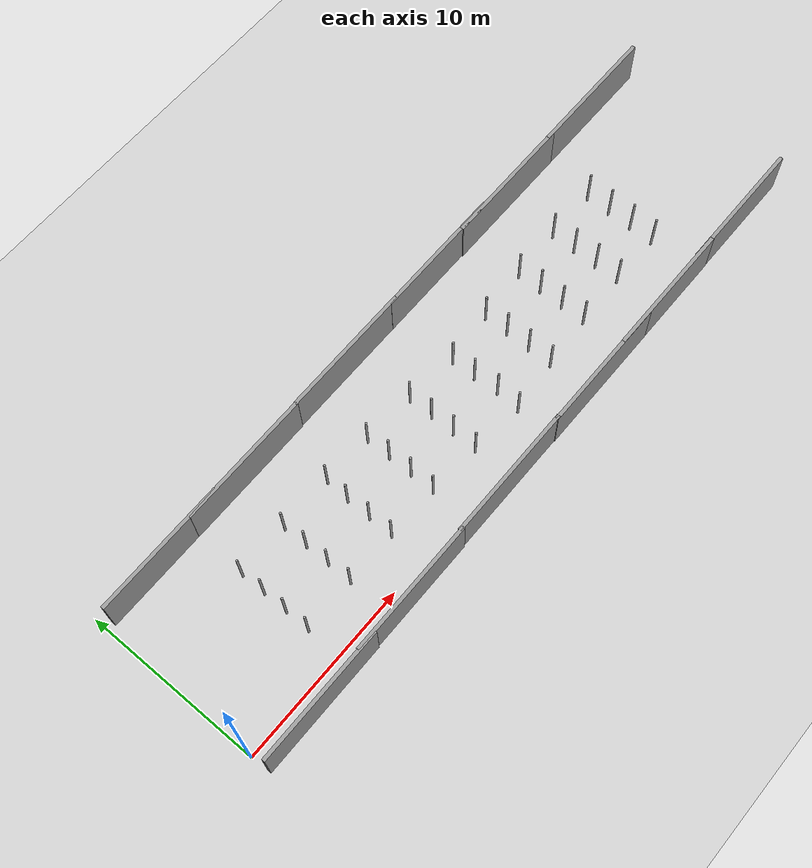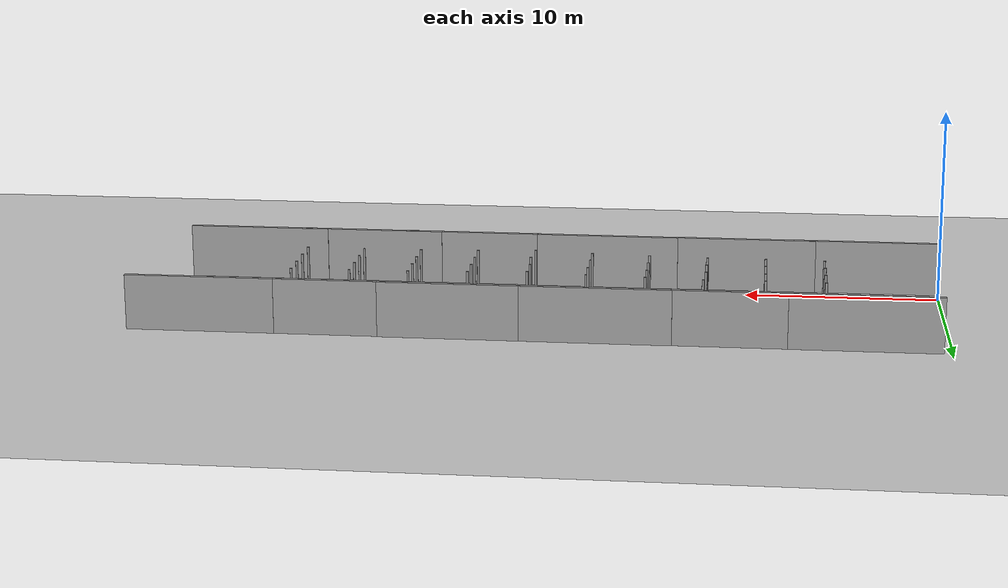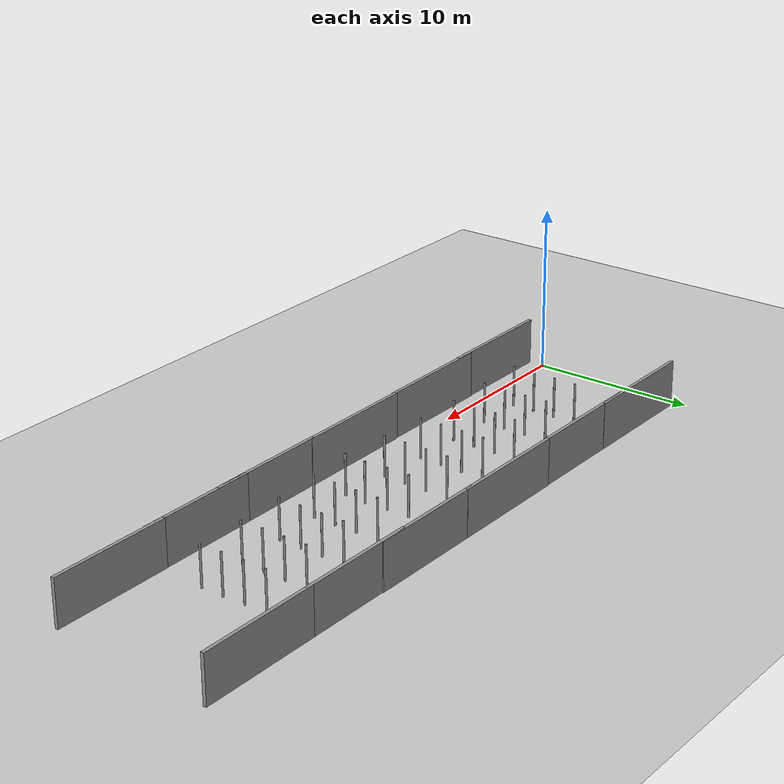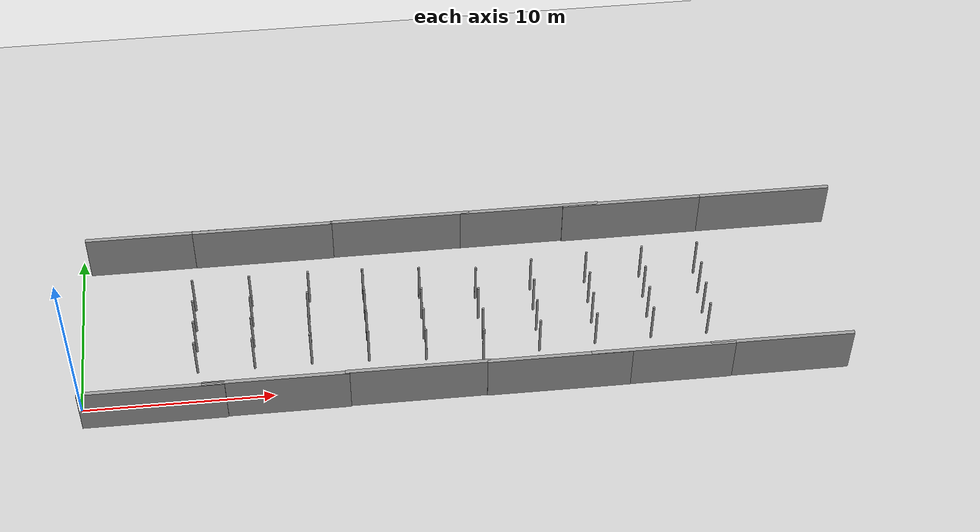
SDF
<sdf version="1.6">
 <world name="default">
  <light name="sun" type="directional">
   <pose>0 0 10 0 -0 0</pose>
   <diffuse>0.8 0.8 0.8 1</diffuse>
   <specular>0.1 0.1 0.1 1</specular>
   <attenuation>
    <range>1000</range>
    <constant>0.9</constant>
    <linear>0.01</linear>
    <quadratic>0.001</quadratic>
   </attenuation>
   <direction>-0.5 0.5 -1</direction>
  </light>
  <model name="ground_plane">
   <static>1</static>
   <link name="link">
    <collision name="collision">
     <geometry><plane><normal>0 0 1</normal><size>100 100</size></plane></geometry>
     <surface><friction><ode><mu>100</mu><mu2>50</mu2></ode></friction></surface>
    </collision>
    <visual name="visual">
     <cast_shadows>0</cast_shadows>
     <geometry><plane><normal>0 0 1</normal><size>100 100</size></plane></geometry>
     <material>
      <script><uri>file://media/materials/scripts/gazebo.material</uri><name>Gazebo/Grey</name></script>
     </material>
    </visual>
   </link>
  </model>
  <gravity>0 0 -9.8</gravity>
  <magnetic_field>6e-06 2.3e-05 -4.2e-05</magnetic_field>
  <atmosphere type="adiabatic"/>
  <physics name="default_physics" default="0" type="ode">
   <max_step_size>0.001</max_step_size>
   <real_time_factor>1</real_time_factor>
   <real_time_update_rate>1000</real_time_update_rate>
  </physics>
  <scene><ambient>0.4 0.4 0.4 1</ambient><background>0.7 0.7 0.7 1</background><shadows>1</shadows></scene>
  <spherical_coordinates>
   <surface_model>EARTH_WGS84</surface_model>
   <latitude_deg>0</latitude_deg>
   <longitude_deg>0</longitude_deg>
   <elevation>0</elevation>
   <heading_deg>0</heading_deg>
  </spherical_coordinates>
  <model name="pole">
   <link name="link_0">
    <inertial>
     <mass>0.0364582</mass>
     <inertia>
      <ixx>0.00312124</ixx>
      <ixy>0</ixy>
      <ixz>0</ixz>
      <iyy>0.00312124</iyy>
      <iyz>0</iyz>
      <izz>0.00016615</izz>
     </inertia>
    </inertial>
    <visual name="visual">
     <geometry><cylinder><radius>0.06</radius><length>2.5</length></cylinder></geometry>
     <material>
      <lighting>1</lighting>
      <script><uri>file://media/materials/scripts/gazebo.material</uri><name>Gazebo/Grey</name></script>
      <ambient>0.3 0.3 0.3 1</ambient>
      <diffuse>0.7 0.7 0.7 1</diffuse>
      <specular>0.01 0.01 0.01 1</specular>
      <emissive>0 0 0 1</emissive>
      <shader type="vertex"><normal_map>__default__</normal_map></shader>
     </material>
    </visual>
    <collision name="collision">
     <geometry><cylinder><radius>0.06</radius><length>2.5</length></cylinder></geometry>
     <surface>
      <friction>
       <ode><mu>1</mu><mu2>1</mu2><fdir1>0 0 0</fdir1><slip1>0</slip1><slip2>0</slip2></ode>
       <torsional>
        <coefficient>1</coefficient>
        <patch_radius>0</patch_radius>
        <surface_radius>0</surface_radius>
        <use_patch_radius>1</use_patch_radius>
        <ode><slip>0</slip></ode>
       </torsional>
      </friction>
      <bounce><restitution_coefficient>0</restitution_coefficient><threshold>1e+06</threshold></bounce>
      <contact>
       <collide_without_contact>0</collide_without_contact>
       <collide_without_contact_bitmask>1</collide_without_contact_bitmask>
       <collide_bitmask>1</collide_bitmask>
       <ode>
        <soft_cfm>0</soft_cfm>
        <soft_erp>0.2</soft_erp>
        <kp>1e+13</kp>
        <kd>1</kd>
        <max_vel>0.01</max_vel>
        <min_depth>0</min_depth>
       </ode>
       <bullet>
        <split_impulse>1</split_impulse>
        <split_impulse_penetration_threshold>-0.01</split_impulse_penetration_threshold>
        <soft_cfm>0</soft_cfm>
        <soft_erp>0.2</soft_erp>
        <kp>1e+13</kp>
        <kd>1</kd>
       </bullet>
      </contact>
     </surface>
    </collision>
   </link>
   <static>0</static>
   <pose>6.00025 1.90193 1.24999 0 1e-06 -0.086409</pose>
  </model>
  <model name="pole_0">
   <link name="link_0">
    <inertial>
     <mass>0.0364582</mass>
     <inertia>
      <ixx>0.00312124</ixx>
      <ixy>0</ixy>
      <ixz>0</ixz>
      <iyy>0.00312124</iyy>
      <iyz>0</iyz>
      <izz>0.00016615</izz>
     </inertia>
    </inertial>
    <visual name="visual">
     <geometry><cylinder><radius>0.06</radius><length>2.5</length></cylinder></geometry>
     <material>
      <lighting>1</lighting>
      <script><uri>file://media/materials/scripts/gazebo.material</uri><name>Gazebo/Grey</name></script>
      <ambient>0.3 0.3 0.3 1</ambient>
      <diffuse>0.7 0.7 0.7 1</diffuse>
      <specular>0.01 0.01 0.01 1</specular>
      <emissive>0 0 0 1</emissive>
      <shader type="vertex"><normal_map>__default__</normal_map></shader>
     </material>
    </visual>
    <collision name="collision">
     <geometry><cylinder><radius>0.06</radius><length>2.5</length></cylinder></geometry>
     <surface>
      <friction>
       <ode><mu>1</mu><mu2>1</mu2><fdir1>0 0 0</fdir1><slip1>0</slip1><slip2>0</slip2></ode>
       <torsional>
        <coefficient>1</coefficient>
        <patch_radius>0</patch_radius>
        <surface_radius>0</surface_radius>
        <use_patch_radius>1</use_patch_radius>
        <ode><slip>0</slip></ode>
       </torsional>
      </friction>
      <bounce><restitution_coefficient>0</restitution_coefficient><threshold>1e+06</threshold></bounce>
      <contact>
       <collide_without_contact>0</collide_without_contact>
       <collide_without_contact_bitmask>1</collide_without_contact_bitmask>
       <collide_bitmask>1</collide_bitmask>
       <ode>
        <soft_cfm>0</soft_cfm>
        <soft_erp>0.2</soft_erp>
        <kp>1e+13</kp>
        <kd>1</kd>
        <max_vel>0.01</max_vel>
        <min_depth>0</min_depth>
       </ode>
       <bullet>
        <split_impulse>1</split_impulse>
        <split_impulse_penetration_threshold>-0.01</split_impulse_penetration_threshold>
        <soft_cfm>0</soft_cfm>
        <soft_erp>0.2</soft_erp>
        <kp>1e+13</kp>
        <kd>1</kd>
       </bullet>
      </contact>
     </surface>
    </collision>
   </link>
   <static>0</static>
   <pose>6.00016 3.30165 1.24999 0 -1e-06 -0.059185</pose>
  </model>
  <model name="pole_1">
   <link name="link_0">
    <inertial>
     <mass>0.0364582</mass>
     <inertia>
      <ixx>0.00312124</ixx>
      <ixy>0</ixy>
      <ixz>0</ixz>
      <iyy>0.00312124</iyy>
      <iyz>0</iyz>
      <izz>0.00016615</izz>
     </inertia>
    </inertial>
    <visual name="visual">
     <geometry><cylinder><radius>0.06</radius><length>2.5</length></cylinder></geometry>
     <material>
      <lighting>1</lighting>
      <script><uri>file://media/materials/scripts/gazebo.material</uri><name>Gazebo/Grey</name></script>
      <ambient>0.3 0.3 0.3 1</ambient>
      <diffuse>0.7 0.7 0.7 1</diffuse>
      <specular>0.01 0.01 0.01 1</specular>
      <emissive>0 0 0 1</emissive>
      <shader type="vertex"><normal_map>__default__</normal_map></shader>
     </material>
    </visual>
    <collision name="collision">
     <geometry><cylinder><radius>0.06</radius><length>2.5</length></cylinder></geometry>
     <surface>
      <friction>
       <ode><mu>1</mu><mu2>1</mu2><fdir1>0 0 0</fdir1><slip1>0</slip1><slip2>0</slip2></ode>
       <torsional>
        <coefficient>1</coefficient>
        <patch_radius>0</patch_radius>
        <surface_radius>0</surface_radius>
        <use_patch_radius>1</use_patch_radius>
        <ode><slip>0</slip></ode>
       </torsional>
      </friction>
      <bounce><restitution_coefficient>0</restitution_coefficient><threshold>1e+06</threshold></bounce>
      <contact>
       <collide_without_contact>0</collide_without_contact>
       <collide_without_contact_bitmask>1</collide_without_contact_bitmask>
       <collide_bitmask>1</collide_bitmask>
       <ode>
        <soft_cfm>0</soft_cfm>
        <soft_erp>0.2</soft_erp>
        <kp>1e+13</kp>
        <kd>1</kd>
        <max_vel>0.01</max_vel>
        <min_depth>0</min_depth>
       </ode>
       <bullet>
        <split_impulse>1</split_impulse>
        <split_impulse_penetration_threshold>-0.01</split_impulse_penetration_threshold>
        <soft_cfm>0</soft_cfm>
        <soft_erp>0.2</soft_erp>
        <kp>1e+13</kp>
        <kd>1</kd>
       </bullet>
      </contact>
     </surface>
    </collision>
   </link>
   <static>0</static>
   <pose>6.00017 4.70128 1.25 -1e-06 -1e-06 -0.059436</pose>
  </model>
  <model name="pole_2">
   <link name="link_0">
    <inertial>
     <mass>0.0364582</mass>
     <inertia>
      <ixx>0.00312124</ixx>
      <ixy>0</ixy>
      <ixz>0</ixz>
      <iyy>0.00312124</iyy>
      <iyz>0</iyz>
      <izz>0.00016615</izz>
     </inertia>
    </inertial>
    <visual name="visual">
     <geometry><cylinder><radius>0.06</radius><length>2.5</length></cylinder></geometry>
     <material>
      <lighting>1</lighting>
      <script><uri>file://media/materials/scripts/gazebo.material</uri><name>Gazebo/Grey</name></script>
      <ambient>0.3 0.3 0.3 1</ambient>
      <diffuse>0.7 0.7 0.7 1</diffuse>
      <specular>0.01 0.01 0.01 1</specular>
      <emissive>0 0 0 1</emissive>
      <shader type="vertex"><normal_map>__default__</normal_map></shader>
     </material>
    </visual>
    <collision name="collision">
     <geometry><cylinder><radius>0.06</radius><length>2.5</length></cylinder></geometry>
     <surface>
      <friction>
       <ode><mu>1</mu><mu2>1</mu2><fdir1>0 0 0</fdir1><slip1>0</slip1><slip2>0</slip2></ode>
       <torsional>
        <coefficient>1</coefficient>
        <patch_radius>0</patch_radius>
        <surface_radius>0</surface_radius>
        <use_patch_radius>1</use_patch_radius>
        <ode><slip>0</slip></ode>
       </torsional>
      </friction>
      <bounce><restitution_coefficient>0</restitution_coefficient><threshold>1e+06</threshold></bounce>
      <contact>
       <collide_without_contact>0</collide_without_contact>
       <collide_without_contact_bitmask>1</collide_without_contact_bitmask>
       <collide_bitmask>1</collide_bitmask>
       <ode>
        <soft_cfm>0</soft_cfm>
        <soft_erp>0.2</soft_erp>
        <kp>1e+13</kp>
        <kd>1</kd>
        <max_vel>0.01</max_vel>
        <min_depth>0</min_depth>
       </ode>
       <bullet>
        <split_impulse>1</split_impulse>
        <split_impulse_penetration_threshold>-0.01</split_impulse_penetration_threshold>
        <soft_cfm>0</soft_cfm>
        <soft_erp>0.2</soft_erp>
        <kp>1e+13</kp>
        <kd>1</kd>
       </bullet>
      </contact>
     </surface>
    </collision>
   </link>
   <static>0</static>
   <pose>6.00019 6.10112 1.24999 -1e-06 1e-06 -0.066745</pose>
  </model>
  <model name="pole_3">
   <link name="link_0">
    <inertial>
     <mass>0.0364582</mass>
     <inertia>
      <ixx>0.00312124</ixx>
      <ixy>0</ixy>
      <ixz>0</ixz>
      <iyy>0.00312124</iyy>
      <iyz>0</iyz>
      <izz>0.00016615</izz>
     </inertia>
    </inertial>
    <visual name="visual">
     <geometry><cylinder><radius>0.06</radius><length>2.5</length></cylinder></geometry>
     <material>
      <lighting>1</lighting>
      <script><uri>file://media/materials/scripts/gazebo.material</uri><name>Gazebo/Grey</name></script>
      <ambient>0.3 0.3 0.3 1</ambient>
      <diffuse>0.7 0.7 0.7 1</diffuse>
      <specular>0.01 0.01 0.01 1</specular>
      <emissive>0 0 0 1</emissive>
      <shader type="vertex"><normal_map>__default__</normal_map></shader>
     </material>
    </visual>
    <collision name="collision">
     <geometry><cylinder><radius>0.06</radius><length>2.5</length></cylinder></geometry>
     <surface>
      <friction>
       <ode><mu>1</mu><mu2>1</mu2><fdir1>0 0 0</fdir1><slip1>0</slip1><slip2>0</slip2></ode>
       <torsional>
        <coefficient>1</coefficient>
        <patch_radius>0</patch_radius>
        <surface_radius>0</surface_radius>
        <use_patch_radius>1</use_patch_radius>
        <ode><slip>0</slip></ode>
       </torsional>
      </friction>
      <bounce><restitution_coefficient>0</restitution_coefficient><threshold>1e+06</threshold></bounce>
      <contact>
       <collide_without_contact>0</collide_without_contact>
       <collide_without_contact_bitmask>1</collide_without_contact_bitmask>
       <collide_bitmask>1</collide_bitmask>
       <ode>
        <soft_cfm>0</soft_cfm>
        <soft_erp>0.2</soft_erp>
        <kp>1e+13</kp>
        <kd>1</kd>
        <max_vel>0.01</max_vel>
        <min_depth>0</min_depth>
       </ode>
       <bullet>
        <split_impulse>1</split_impulse>
        <split_impulse_penetration_threshold>-0.01</split_impulse_penetration_threshold>
        <soft_cfm>0</soft_cfm>
        <soft_erp>0.2</soft_erp>
        <kp>1e+13</kp>
        <kd>1</kd>
       </bullet>
      </contact>
     </surface>
    </collision>
   </link>
   <static>0</static>
   <pose>12.0002 1.90167 1.24999 -1e-06 -0 -0.059461</pose>
  </model>
  <model name="pole_4">
   <link name="link_0">
    <inertial>
     <mass>0.0364582</mass>
     <inertia>
      <ixx>0.00312124</ixx>
      <ixy>0</ixy>
      <ixz>0</ixz>
      <iyy>0.00312124</iyy>
      <iyz>0</iyz>
      <izz>0.00016615</izz>
     </inertia>
    </inertial>
    <visual name="visual">
     <geometry><cylinder><radius>0.06</radius><length>2.5</length></cylinder></geometry>
     <material>
      <lighting>1</lighting>
      <script><uri>file://media/materials/scripts/gazebo.material</uri><name>Gazebo/Grey</name></script>
      <ambient>0.3 0.3 0.3 1</ambient>
      <diffuse>0.7 0.7 0.7 1</diffuse>
      <specular>0.01 0.01 0.01 1</specular>
      <emissive>0 0 0 1</emissive>
      <shader type="vertex"><normal_map>__default__</normal_map></shader>
     </material>
    </visual>
    <collision name="collision">
     <geometry><cylinder><radius>0.06</radius><length>2.5</length></cylinder></geometry>
     <surface>
      <friction>
       <ode><mu>1</mu><mu2>1</mu2><fdir1>0 0 0</fdir1><slip1>0</slip1><slip2>0</slip2></ode>
       <torsional>
        <coefficient>1</coefficient>
        <patch_radius>0</patch_radius>
        <surface_radius>0</surface_radius>
        <use_patch_radius>1</use_patch_radius>
        <ode><slip>0</slip></ode>
       </torsional>
      </friction>
      <bounce><restitution_coefficient>0</restitution_coefficient><threshold>1e+06</threshold></bounce>
      <contact>
       <collide_without_contact>0</collide_without_contact>
       <collide_without_contact_bitmask>1</collide_without_contact_bitmask>
       <collide_bitmask>1</collide_bitmask>
       <ode>
        <soft_cfm>0</soft_cfm>
        <soft_erp>0.2</soft_erp>
        <kp>1e+13</kp>
        <kd>1</kd>
        <max_vel>0.01</max_vel>
        <min_depth>0</min_depth>
       </ode>
       <bullet>
        <split_impulse>1</split_impulse>
        <split_impulse_penetration_threshold>-0.01</split_impulse_penetration_threshold>
        <soft_cfm>0</soft_cfm>
        <soft_erp>0.2</soft_erp>
        <kp>1e+13</kp>
        <kd>1</kd>
       </bullet>
      </contact>
     </surface>
    </collision>
   </link>
   <static>0</static>
   <pose>9.00014 3.30162 1.24999 -1e-06 1e-06 -0.05632</pose>
  </model>
  <model name="pole_5">
   <link name="link_0">
    <inertial>
     <mass>0.0364582</mass>
     <inertia>
      <ixx>0.00312124</ixx>
      <ixy>0</ixy>
      <ixz>0</ixz>
      <iyy>0.00312124</iyy>
      <iyz>0</iyz>
      <izz>0.00016615</izz>
     </inertia>
    </inertial>
    <visual name="visual">
     <geometry><cylinder><radius>0.06</radius><length>2.5</length></cylinder></geometry>
     <material>
      <lighting>1</lighting>
      <script><uri>file://media/materials/scripts/gazebo.material</uri><name>Gazebo/Grey</name></script>
      <ambient>0.3 0.3 0.3 1</ambient>
      <diffuse>0.7 0.7 0.7 1</diffuse>
      <specular>0.01 0.01 0.01 1</specular>
      <emissive>0 0 0 1</emissive>
      <shader type="vertex"><normal_map>__default__</normal_map></shader>
     </material>
    </visual>
    <collision name="collision">
     <geometry><cylinder><radius>0.06</radius><length>2.5</length></cylinder></geometry>
     <surface>
      <friction>
       <ode><mu>1</mu><mu2>1</mu2><fdir1>0 0 0</fdir1><slip1>0</slip1><slip2>0</slip2></ode>
       <torsional>
        <coefficient>1</coefficient>
        <patch_radius>0</patch_radius>
        <surface_radius>0</surface_radius>
        <use_patch_radius>1</use_patch_radius>
        <ode><slip>0</slip></ode>
       </torsional>
      </friction>
      <bounce><restitution_coefficient>0</restitution_coefficient><threshold>1e+06</threshold></bounce>
      <contact>
       <collide_without_contact>0</collide_without_contact>
       <collide_without_contact_bitmask>1</collide_without_contact_bitmask>
       <collide_bitmask>1</collide_bitmask>
       <ode>
        <soft_cfm>0</soft_cfm>
        <soft_erp>0.2</soft_erp>
        <kp>1e+13</kp>
        <kd>1</kd>
        <max_vel>0.01</max_vel>
        <min_depth>0</min_depth>
       </ode>
       <bullet>
        <split_impulse>1</split_impulse>
        <split_impulse_penetration_threshold>-0.01</split_impulse_penetration_threshold>
        <soft_cfm>0</soft_cfm>
        <soft_erp>0.2</soft_erp>
        <kp>1e+13</kp>
        <kd>1</kd>
       </bullet>
      </contact>
     </surface>
    </collision>
   </link>
   <static>0</static>
   <pose>9.00017 4.70125 1.24999 -1e-06 1e-06 -0.058881</pose>
  </model>
  <model name="pole_6">
   <link name="link_0">
    <inertial>
     <mass>0.0364582</mass>
     <inertia>
      <ixx>0.00312124</ixx>
      <ixy>0</ixy>
      <ixz>0</ixz>
      <iyy>0.00312124</iyy>
      <iyz>0</iyz>
      <izz>0.00016615</izz>
     </inertia>
    </inertial>
    <visual name="visual">
     <geometry><cylinder><radius>0.06</radius><length>2.5</length></cylinder></geometry>
     <material>
      <lighting>1</lighting>
      <script><uri>file://media/materials/scripts/gazebo.material</uri><name>Gazebo/Grey</name></script>
      <ambient>0.3 0.3 0.3 1</ambient>
      <diffuse>0.7 0.7 0.7 1</diffuse>
      <specular>0.01 0.01 0.01 1</specular>
      <emissive>0 0 0 1</emissive>
      <shader type="vertex"><normal_map>__default__</normal_map></shader>
     </material>
    </visual>
    <collision name="collision">
     <geometry><cylinder><radius>0.06</radius><length>2.5</length></cylinder></geometry>
     <surface>
      <friction>
       <ode><mu>1</mu><mu2>1</mu2><fdir1>0 0 0</fdir1><slip1>0</slip1><slip2>0</slip2></ode>
       <torsional>
        <coefficient>1</coefficient>
        <patch_radius>0</patch_radius>
        <surface_radius>0</surface_radius>
        <use_patch_radius>1</use_patch_radius>
        <ode><slip>0</slip></ode>
       </torsional>
      </friction>
      <bounce><restitution_coefficient>0</restitution_coefficient><threshold>1e+06</threshold></bounce>
      <contact>
       <collide_without_contact>0</collide_without_contact>
       <collide_without_contact_bitmask>1</collide_without_contact_bitmask>
       <collide_bitmask>1</collide_bitmask>
       <ode>
        <soft_cfm>0</soft_cfm>
        <soft_erp>0.2</soft_erp>
        <kp>1e+13</kp>
        <kd>1</kd>
        <max_vel>0.01</max_vel>
        <min_depth>0</min_depth>
       </ode>
       <bullet>
        <split_impulse>1</split_impulse>
        <split_impulse_penetration_threshold>-0.01</split_impulse_penetration_threshold>
        <soft_cfm>0</soft_cfm>
        <soft_erp>0.2</soft_erp>
        <kp>1e+13</kp>
        <kd>1</kd>
       </bullet>
      </contact>
     </surface>
    </collision>
   </link>
   <static>0</static>
   <pose>9.00015 6.10129 1.25 -1e-06 -1e-06 -0.078964</pose>
  </model>
  <model name="pole_7">
   <link name="link_0">
    <inertial>
     <mass>0.0364582</mass>
     <inertia>
      <ixx>0.00312124</ixx>
      <ixy>0</ixy>
      <ixz>0</ixz>
      <iyy>0.00312124</iyy>
      <iyz>0</iyz>
      <izz>0.00016615</izz>
     </inertia>
    </inertial>
    <visual name="visual">
     <geometry><cylinder><radius>0.06</radius><length>2.5</length></cylinder></geometry>
     <material>
      <lighting>1</lighting>
      <script><uri>file://media/materials/scripts/gazebo.material</uri><name>Gazebo/Grey</name></script>
      <ambient>0.3 0.3 0.3 1</ambient>
      <diffuse>0.7 0.7 0.7 1</diffuse>
      <specular>0.01 0.01 0.01 1</specular>
      <emissive>0 0 0 1</emissive>
      <shader type="vertex"><normal_map>__default__</normal_map></shader>
     </material>
    </visual>
    <collision name="collision">
     <geometry><cylinder><radius>0.06</radius><length>2.5</length></cylinder></geometry>
     <surface>
      <friction>
       <ode><mu>1</mu><mu2>1</mu2><fdir1>0 0 0</fdir1><slip1>0</slip1><slip2>0</slip2></ode>
       <torsional>
        <coefficient>1</coefficient>
        <patch_radius>0</patch_radius>
        <surface_radius>0</surface_radius>
        <use_patch_radius>1</use_patch_radius>
        <ode><slip>0</slip></ode>
       </torsional>
      </friction>
      <bounce><restitution_coefficient>0</restitution_coefficient><threshold>1e+06</threshold></bounce>
      <contact>
       <collide_without_contact>0</collide_without_contact>
       <collide_without_contact_bitmask>1</collide_without_contact_bitmask>
       <collide_bitmask>1</collide_bitmask>
       <ode>
        <soft_cfm>0</soft_cfm>
        <soft_erp>0.2</soft_erp>
        <kp>1e+13</kp>
        <kd>1</kd>
        <max_vel>0.01</max_vel>
        <min_depth>0</min_depth>
       </ode>
       <bullet>
        <split_impulse>1</split_impulse>
        <split_impulse_penetration_threshold>-0.01</split_impulse_penetration_threshold>
        <soft_cfm>0</soft_cfm>
        <soft_erp>0.2</soft_erp>
        <kp>1e+13</kp>
        <kd>1</kd>
       </bullet>
      </contact>
     </surface>
    </collision>
   </link>
   <static>0</static>
   <pose>9.00026 1.90181 1.25 0 -1e-06 -0.052308</pose>
  </model>
  <model name="pole_8">
   <link name="link_0">
    <inertial>
     <mass>0.0364582</mass>
     <inertia>
      <ixx>0.00312124</ixx>
      <ixy>0</ixy>
      <ixz>0</ixz>
      <iyy>0.00312124</iyy>
      <iyz>0</iyz>
      <izz>0.00016615</izz>
     </inertia>
    </inertial>
    <visual name="visual">
     <geometry><cylinder><radius>0.06</radius><length>2.5</length></cylinder></geometry>
     <material>
      <lighting>1</lighting>
      <script><uri>file://media/materials/scripts/gazebo.material</uri><name>Gazebo/Grey</name></script>
      <ambient>0.3 0.3 0.3 1</ambient>
      <diffuse>0.7 0.7 0.7 1</diffuse>
      <specular>0.01 0.01 0.01 1</specular>
      <emissive>0 0 0 1</emissive>
      <shader type="vertex"><normal_map>__default__</normal_map></shader>
     </material>
    </visual>
    <collision name="collision">
     <geometry><cylinder><radius>0.06</radius><length>2.5</length></cylinder></geometry>
     <surface>
      <friction>
       <ode><mu>1</mu><mu2>1</mu2><fdir1>0 0 0</fdir1><slip1>0</slip1><slip2>0</slip2></ode>
       <torsional>
        <coefficient>1</coefficient>
        <patch_radius>0</patch_radius>
        <surface_radius>0</surface_radius>
        <use_patch_radius>1</use_patch_radius>
        <ode><slip>0</slip></ode>
       </torsional>
      </friction>
      <bounce><restitution_coefficient>0</restitution_coefficient><threshold>1e+06</threshold></bounce>
      <contact>
       <collide_without_contact>0</collide_without_contact>
       <collide_without_contact_bitmask>1</collide_without_contact_bitmask>
       <collide_bitmask>1</collide_bitmask>
       <ode>
        <soft_cfm>0</soft_cfm>
        <soft_erp>0.2</soft_erp>
        <kp>1e+13</kp>
        <kd>1</kd>
        <max_vel>0.01</max_vel>
        <min_depth>0</min_depth>
       </ode>
       <bullet>
        <split_impulse>1</split_impulse>
        <split_impulse_penetration_threshold>-0.01</split_impulse_penetration_threshold>
        <soft_cfm>0</soft_cfm>
        <soft_erp>0.2</soft_erp>
        <kp>1e+13</kp>
        <kd>1</kd>
       </bullet>
      </contact>
     </surface>
    </collision>
   </link>
   <static>0</static>
   <pose>12.0002 3.30152 1.24999 0 -1e-06 -0.054215</pose>
  </model>
  <model name="pole_9">
   <link name="link_0">
    <inertial>
     <mass>0.0364582</mass>
     <inertia>
      <ixx>0.00312124</ixx>
      <ixy>0</ixy>
      <ixz>0</ixz>
      <iyy>0.00312124</iyy>
      <iyz>0</iyz>
      <izz>0.00016615</izz>
     </inertia>
    </inertial>
    <visual name="visual">
     <geometry><cylinder><radius>0.06</radius><length>2.5</length></cylinder></geometry>
     <material>
      <lighting>1</lighting>
      <script><uri>file://media/materials/scripts/gazebo.material</uri><name>Gazebo/Grey</name></script>
      <ambient>0.3 0.3 0.3 1</ambient>
      <diffuse>0.7 0.7 0.7 1</diffuse>
      <specular>0.01 0.01 0.01 1</specular>
      <emissive>0 0 0 1</emissive>
      <shader type="vertex"><normal_map>__default__</normal_map></shader>
     </material>
    </visual>
    <collision name="collision">
     <geometry><cylinder><radius>0.06</radius><length>2.5</length></cylinder></geometry>
     <surface>
      <friction>
       <ode><mu>1</mu><mu2>1</mu2><fdir1>0 0 0</fdir1><slip1>0</slip1><slip2>0</slip2></ode>
       <torsional>
        <coefficient>1</coefficient>
        <patch_radius>0</patch_radius>
        <surface_radius>0</surface_radius>
        <use_patch_radius>1</use_patch_radius>
        <ode><slip>0</slip></ode>
       </torsional>
      </friction>
      <bounce><restitution_coefficient>0</restitution_coefficient><threshold>1e+06</threshold></bounce>
      <contact>
       <collide_without_contact>0</collide_without_contact>
       <collide_without_contact_bitmask>1</collide_without_contact_bitmask>
       <collide_bitmask>1</collide_bitmask>
       <ode>
        <soft_cfm>0</soft_cfm>
        <soft_erp>0.2</soft_erp>
        <kp>1e+13</kp>
        <kd>1</kd>
        <max_vel>0.01</max_vel>
        <min_depth>0</min_depth>
       </ode>
       <bullet>
        <split_impulse>1</split_impulse>
        <split_impulse_penetration_threshold>-0.01</split_impulse_penetration_threshold>
        <soft_cfm>0</soft_cfm>
        <soft_erp>0.2</soft_erp>
        <kp>1e+13</kp>
        <kd>1</kd>
       </bullet>
      </contact>
     </surface>
    </collision>
   </link>
   <static>0</static>
   <pose>12.0002 4.70116 1.25 0 1e-06 -0.058336</pose>
  </model>
  <model name="pole_10">
   <link name="link_0">
    <inertial>
     <mass>0.0364582</mass>
     <inertia>
      <ixx>0.00312124</ixx>
      <ixy>0</ixy>
      <ixz>0</ixz>
      <iyy>0.00312124</iyy>
      <iyz>0</iyz>
      <izz>0.00016615</izz>
     </inertia>
    </inertial>
    <visual name="visual">
     <geometry><cylinder><radius>0.06</radius><length>2.5</length></cylinder></geometry>
     <material>
      <lighting>1</lighting>
      <script><uri>file://media/materials/scripts/gazebo.material</uri><name>Gazebo/Grey</name></script>
      <ambient>0.3 0.3 0.3 1</ambient>
      <diffuse>0.7 0.7 0.7 1</diffuse>
      <specular>0.01 0.01 0.01 1</specular>
      <emissive>0 0 0 1</emissive>
      <shader type="vertex"><normal_map>__default__</normal_map></shader>
     </material>
    </visual>
    <collision name="collision">
     <geometry><cylinder><radius>0.06</radius><length>2.5</length></cylinder></geometry>
     <surface>
      <friction>
       <ode><mu>1</mu><mu2>1</mu2><fdir1>0 0 0</fdir1><slip1>0</slip1><slip2>0</slip2></ode>
       <torsional>
        <coefficient>1</coefficient>
        <patch_radius>0</patch_radius>
        <surface_radius>0</surface_radius>
        <use_patch_radius>1</use_patch_radius>
        <ode><slip>0</slip></ode>
       </torsional>
      </friction>
      <bounce><restitution_coefficient>0</restitution_coefficient><threshold>1e+06</threshold></bounce>
      <contact>
       <collide_without_contact>0</collide_without_contact>
       <collide_without_contact_bitmask>1</collide_without_contact_bitmask>
       <collide_bitmask>1</collide_bitmask>
       <ode>
        <soft_cfm>0</soft_cfm>
        <soft_erp>0.2</soft_erp>
        <kp>1e+13</kp>
        <kd>1</kd>
        <max_vel>0.01</max_vel>
        <min_depth>0</min_depth>
       </ode>
       <bullet>
        <split_impulse>1</split_impulse>
        <split_impulse_penetration_threshold>-0.01</split_impulse_penetration_threshold>
        <soft_cfm>0</soft_cfm>
        <soft_erp>0.2</soft_erp>
        <kp>1e+13</kp>
        <kd>1</kd>
       </bullet>
      </contact>
     </surface>
    </collision>
   </link>
   <static>0</static>
   <pose>12.1071 6.10119 1.25 -0 1e-06 -0.055066</pose>
  </model>
  <model name="pole_11">
   <link name="link_0">
    <inertial>
     <mass>0.0364582</mass>
     <inertia>
      <ixx>0.00312124</ixx>
      <ixy>0</ixy>
      <ixz>0</ixz>
      <iyy>0.00312124</iyy>
      <iyz>0</iyz>
      <izz>0.00016615</izz>
     </inertia>
    </inertial>
    <visual name="visual">
     <geometry><cylinder><radius>0.06</radius><length>2.5</length></cylinder></geometry>
     <material>
      <lighting>1</lighting>
      <script><uri>file://media/materials/scripts/gazebo.material</uri><name>Gazebo/Grey</name></script>
      <ambient>0.3 0.3 0.3 1</ambient>
      <diffuse>0.7 0.7 0.7 1</diffuse>
      <specular>0.01 0.01 0.01 1</specular>
      <emissive>0 0 0 1</emissive>
      <shader type="vertex"><normal_map>__default__</normal_map></shader>
     </material>
    </visual>
    <collision name="collision">
     <geometry><cylinder><radius>0.06</radius><length>2.5</length></cylinder></geometry>
     <surface>
      <friction>
       <ode><mu>1</mu><mu2>1</mu2><fdir1>0 0 0</fdir1><slip1>0</slip1><slip2>0</slip2></ode>
       <torsional>
        <coefficient>1</coefficient>
        <patch_radius>0</patch_radius>
        <surface_radius>0</surface_radius>
        <use_patch_radius>1</use_patch_radius>
        <ode><slip>0</slip></ode>
       </torsional>
      </friction>
      <bounce><restitution_coefficient>0</restitution_coefficient><threshold>1e+06</threshold></bounce>
      <contact>
       <collide_without_contact>0</collide_without_contact>
       <collide_without_contact_bitmask>1</collide_without_contact_bitmask>
       <collide_bitmask>1</collide_bitmask>
       <ode>
        <soft_cfm>0</soft_cfm>
        <soft_erp>0.2</soft_erp>
        <kp>1e+13</kp>
        <kd>1</kd>
        <max_vel>0.01</max_vel>
        <min_depth>0</min_depth>
       </ode>
       <bullet>
        <split_impulse>1</split_impulse>
        <split_impulse_penetration_threshold>-0.01</split_impulse_penetration_threshold>
        <soft_cfm>0</soft_cfm>
        <soft_erp>0.2</soft_erp>
        <kp>1e+13</kp>
        <kd>1</kd>
       </bullet>
      </contact>
     </surface>
    </collision>
   </link>
   <static>0</static>
   <pose>15.0002 1.80129 1.24999 -1e-06 1e-06 -0.051988</pose>
  </model>
  <model name="pole_12">
   <link name="link_0">
    <inertial>
     <mass>0.0364582</mass>
     <inertia>
      <ixx>0.00312124</ixx>
      <ixy>0</ixy>
      <ixz>0</ixz>
      <iyy>0.00312124</iyy>
      <iyz>0</iyz>
      <izz>0.00016615</izz>
     </inertia>
    </inertial>
    <visual name="visual">
     <geometry><cylinder><radius>0.06</radius><length>2.5</length></cylinder></geometry>
     <material>
      <lighting>1</lighting>
      <script><uri>file://media/materials/scripts/gazebo.material</uri><name>Gazebo/Grey</name></script>
      <ambient>0.3 0.3 0.3 1</ambient>
      <diffuse>0.7 0.7 0.7 1</diffuse>
      <specular>0.01 0.01 0.01 1</specular>
      <emissive>0 0 0 1</emissive>
      <shader type="vertex"><normal_map>__default__</normal_map></shader>
     </material>
    </visual>
    <collision name="collision">
     <geometry><cylinder><radius>0.06</radius><length>2.5</length></cylinder></geometry>
     <surface>
      <friction>
       <ode><mu>1</mu><mu2>1</mu2><fdir1>0 0 0</fdir1><slip1>0</slip1><slip2>0</slip2></ode>
       <torsional>
        <coefficient>1</coefficient>
        <patch_radius>0</patch_radius>
        <surface_radius>0</surface_radius>
        <use_patch_radius>1</use_patch_radius>
        <ode><slip>0</slip></ode>
       </torsional>
      </friction>
      <bounce><restitution_coefficient>0</restitution_coefficient><threshold>1e+06</threshold></bounce>
      <contact>
       <collide_without_contact>0</collide_without_contact>
       <collide_without_contact_bitmask>1</collide_without_contact_bitmask>
       <collide_bitmask>1</collide_bitmask>
       <ode>
        <soft_cfm>0</soft_cfm>
        <soft_erp>0.2</soft_erp>
        <kp>1e+13</kp>
        <kd>1</kd>
        <max_vel>0.01</max_vel>
        <min_depth>0</min_depth>
       </ode>
       <bullet>
        <split_impulse>1</split_impulse>
        <split_impulse_penetration_threshold>-0.01</split_impulse_penetration_threshold>
        <soft_cfm>0</soft_cfm>
        <soft_erp>0.2</soft_erp>
        <kp>1e+13</kp>
        <kd>1</kd>
       </bullet>
      </contact>
     </surface>
    </collision>
   </link>
   <static>0</static>
   <pose>18.0002 1.60177 1.25 0 1e-06 -0.053116</pose>
  </model>
  <model name="pole_13">
   <link name="link_0">
    <inertial>
     <mass>0.0364582</mass>
     <inertia>
      <ixx>0.00312124</ixx>
      <ixy>0</ixy>
      <ixz>0</ixz>
      <iyy>0.00312124</iyy>
      <iyz>0</iyz>
      <izz>0.00016615</izz>
     </inertia>
    </inertial>
    <visual name="visual">
     <geometry><cylinder><radius>0.06</radius><length>2.5</length></cylinder></geometry>
     <material>
      <lighting>1</lighting>
      <script><uri>file://media/materials/scripts/gazebo.material</uri><name>Gazebo/Grey</name></script>
      <ambient>0.3 0.3 0.3 1</ambient>
      <diffuse>0.7 0.7 0.7 1</diffuse>
      <specular>0.01 0.01 0.01 1</specular>
      <emissive>0 0 0 1</emissive>
      <shader type="vertex"><normal_map>__default__</normal_map></shader>
     </material>
    </visual>
    <collision name="collision">
     <geometry><cylinder><radius>0.06</radius><length>2.5</length></cylinder></geometry>
     <surface>
      <friction>
       <ode><mu>1</mu><mu2>1</mu2><fdir1>0 0 0</fdir1><slip1>0</slip1><slip2>0</slip2></ode>
       <torsional>
        <coefficient>1</coefficient>
        <patch_radius>0</patch_radius>
        <surface_radius>0</surface_radius>
        <use_patch_radius>1</use_patch_radius>
        <ode><slip>0</slip></ode>
       </torsional>
      </friction>
      <bounce><restitution_coefficient>0</restitution_coefficient><threshold>1e+06</threshold></bounce>
      <contact>
       <collide_without_contact>0</collide_without_contact>
       <collide_without_contact_bitmask>1</collide_without_contact_bitmask>
       <collide_bitmask>1</collide_bitmask>
       <ode>
        <soft_cfm>0</soft_cfm>
        <soft_erp>0.2</soft_erp>
        <kp>1e+13</kp>
        <kd>1</kd>
        <max_vel>0.01</max_vel>
        <min_depth>0</min_depth>
       </ode>
       <bullet>
        <split_impulse>1</split_impulse>
        <split_impulse_penetration_threshold>-0.01</split_impulse_penetration_threshold>
        <soft_cfm>0</soft_cfm>
        <soft_erp>0.2</soft_erp>
        <kp>1e+13</kp>
        <kd>1</kd>
       </bullet>
      </contact>
     </surface>
    </collision>
   </link>
   <static>0</static>
   <pose>21.0002 1.30174 1.25 -1e-06 1e-06 -0.05392</pose>
  </model>
  <model name="pole_14">
   <link name="link_0">
    <inertial>
     <mass>0.0364582</mass>
     <inertia>
      <ixx>0.00312124</ixx>
      <ixy>0</ixy>
      <ixz>0</ixz>
      <iyy>0.00312124</iyy>
      <iyz>0</iyz>
      <izz>0.00016615</izz>
     </inertia>
    </inertial>
    <visual name="visual">
     <geometry><cylinder><radius>0.06</radius><length>2.5</length></cylinder></geometry>
     <material>
      <lighting>1</lighting>
      <script><uri>file://media/materials/scripts/gazebo.material</uri><name>Gazebo/Grey</name></script>
      <ambient>0.3 0.3 0.3 1</ambient>
      <diffuse>0.7 0.7 0.7 1</diffuse>
      <specular>0.01 0.01 0.01 1</specular>
      <emissive>0 0 0 1</emissive>
      <shader type="vertex"><normal_map>__default__</normal_map></shader>
     </material>
    </visual>
    <collision name="collision">
     <geometry><cylinder><radius>0.06</radius><length>2.5</length></cylinder></geometry>
     <surface>
      <friction>
       <ode><mu>1</mu><mu2>1</mu2><fdir1>0 0 0</fdir1><slip1>0</slip1><slip2>0</slip2></ode>
       <torsional>
        <coefficient>1</coefficient>
        <patch_radius>0</patch_radius>
        <surface_radius>0</surface_radius>
        <use_patch_radius>1</use_patch_radius>
        <ode><slip>0</slip></ode>
       </torsional>
      </friction>
      <bounce><restitution_coefficient>0</restitution_coefficient><threshold>1e+06</threshold></bounce>
      <contact>
       <collide_without_contact>0</collide_without_contact>
       <collide_without_contact_bitmask>1</collide_without_contact_bitmask>
       <collide_bitmask>1</collide_bitmask>
       <ode>
        <soft_cfm>0</soft_cfm>
        <soft_erp>0.2</soft_erp>
        <kp>1e+13</kp>
        <kd>1</kd>
        <max_vel>0.01</max_vel>
        <min_depth>0</min_depth>
       </ode>
       <bullet>
        <split_impulse>1</split_impulse>
        <split_impulse_penetration_threshold>-0.01</split_impulse_penetration_threshold>
        <soft_cfm>0</soft_cfm>
        <soft_erp>0.2</soft_erp>
        <kp>1e+13</kp>
        <kd>1</kd>
       </bullet>
      </contact>
     </surface>
    </collision>
   </link>
   <static>0</static>
   <pose>15.0002 3.20142 1.25 -1e-06 -1e-06 -0.027402</pose>
  </model>
  <model name="pole_15">
   <link name="link_0">
    <inertial>
     <mass>0.0364582</mass>
     <inertia>
      <ixx>0.00312124</ixx>
      <ixy>0</ixy>
      <ixz>0</ixz>
      <iyy>0.00312124</iyy>
      <iyz>0</iyz>
      <izz>0.00016615</izz>
     </inertia>
    </inertial>
    <visual name="visual">
     <geometry><cylinder><radius>0.06</radius><length>2.5</length></cylinder></geometry>
     <material>
      <lighting>1</lighting>
      <script><uri>file://media/materials/scripts/gazebo.material</uri><name>Gazebo/Grey</name></script>
      <ambient>0.3 0.3 0.3 1</ambient>
      <diffuse>0.7 0.7 0.7 1</diffuse>
      <specular>0.01 0.01 0.01 1</specular>
      <emissive>0 0 0 1</emissive>
      <shader type="vertex"><normal_map>__default__</normal_map></shader>
     </material>
    </visual>
    <collision name="collision">
     <geometry><cylinder><radius>0.06</radius><length>2.5</length></cylinder></geometry>
     <surface>
      <friction>
       <ode><mu>1</mu><mu2>1</mu2><fdir1>0 0 0</fdir1><slip1>0</slip1><slip2>0</slip2></ode>
       <torsional>
        <coefficient>1</coefficient>
        <patch_radius>0</patch_radius>
        <surface_radius>0</surface_radius>
        <use_patch_radius>1</use_patch_radius>
        <ode><slip>0</slip></ode>
       </torsional>
      </friction>
      <bounce><restitution_coefficient>0</restitution_coefficient><threshold>1e+06</threshold></bounce>
      <contact>
       <collide_without_contact>0</collide_without_contact>
       <collide_without_contact_bitmask>1</collide_without_contact_bitmask>
       <collide_bitmask>1</collide_bitmask>
       <ode>
        <soft_cfm>0</soft_cfm>
        <soft_erp>0.2</soft_erp>
        <kp>1e+13</kp>
        <kd>1</kd>
        <max_vel>0.01</max_vel>
        <min_depth>0</min_depth>
       </ode>
       <bullet>
        <split_impulse>1</split_impulse>
        <split_impulse_penetration_threshold>-0.01</split_impulse_penetration_threshold>
        <soft_cfm>0</soft_cfm>
        <soft_erp>0.2</soft_erp>
        <kp>1e+13</kp>
        <kd>1</kd>
       </bullet>
      </contact>
     </surface>
    </collision>
   </link>
   <static>0</static>
   <pose>18.0002 3.00143 1.24999 -1e-06 -0 0.034978</pose>
  </model>
  <model name="pole_16">
   <link name="link_0">
    <inertial>
     <mass>0.0364582</mass>
     <inertia>
      <ixx>0.00312124</ixx>
      <ixy>0</ixy>
      <ixz>0</ixz>
      <iyy>0.00312124</iyy>
      <iyz>0</iyz>
      <izz>0.00016615</izz>
     </inertia>
    </inertial>
    <visual name="visual">
     <geometry><cylinder><radius>0.06</radius><length>2.5</length></cylinder></geometry>
     <material>
      <lighting>1</lighting>
      <script><uri>file://media/materials/scripts/gazebo.material</uri><name>Gazebo/Grey</name></script>
      <ambient>0.3 0.3 0.3 1</ambient>
      <diffuse>0.7 0.7 0.7 1</diffuse>
      <specular>0.01 0.01 0.01 1</specular>
      <emissive>0 0 0 1</emissive>
      <shader type="vertex"><normal_map>__default__</normal_map></shader>
     </material>
    </visual>
    <collision name="collision">
     <geometry><cylinder><radius>0.06</radius><length>2.5</length></cylinder></geometry>
     <surface>
      <friction>
       <ode><mu>1</mu><mu2>1</mu2><fdir1>0 0 0</fdir1><slip1>0</slip1><slip2>0</slip2></ode>
       <torsional>
        <coefficient>1</coefficient>
        <patch_radius>0</patch_radius>
        <surface_radius>0</surface_radius>
        <use_patch_radius>1</use_patch_radius>
        <ode><slip>0</slip></ode>
       </torsional>
      </friction>
      <bounce><restitution_coefficient>0</restitution_coefficient><threshold>1e+06</threshold></bounce>
      <contact>
       <collide_without_contact>0</collide_without_contact>
       <collide_without_contact_bitmask>1</collide_without_contact_bitmask>
       <collide_bitmask>1</collide_bitmask>
       <ode>
        <soft_cfm>0</soft_cfm>
        <soft_erp>0.2</soft_erp>
        <kp>1e+13</kp>
        <kd>1</kd>
        <max_vel>0.01</max_vel>
        <min_depth>0</min_depth>
       </ode>
       <bullet>
        <split_impulse>1</split_impulse>
        <split_impulse_penetration_threshold>-0.01</split_impulse_penetration_threshold>
        <soft_cfm>0</soft_cfm>
        <soft_erp>0.2</soft_erp>
        <kp>1e+13</kp>
        <kd>1</kd>
       </bullet>
      </contact>
     </surface>
    </collision>
   </link>
   <static>0</static>
   <pose>21.1078 2.7014 1.24999 -1e-06 -1e-06 0.018883</pose>
  </model>
  <model name="pole_17">
   <link name="link_0">
    <inertial>
     <mass>0.0364582</mass>
     <inertia>
      <ixx>0.00312124</ixx>
      <ixy>0</ixy>
      <ixz>0</ixz>
      <iyy>0.00312124</iyy>
      <iyz>0</iyz>
      <izz>0.00016615</izz>
     </inertia>
    </inertial>
    <visual name="visual">
     <geometry><cylinder><radius>0.06</radius><length>2.5</length></cylinder></geometry>
     <material>
      <lighting>1</lighting>
      <script><uri>file://media/materials/scripts/gazebo.material</uri><name>Gazebo/Grey</name></script>
      <ambient>0.3 0.3 0.3 1</ambient>
      <diffuse>0.7 0.7 0.7 1</diffuse>
      <specular>0.01 0.01 0.01 1</specular>
      <emissive>0 0 0 1</emissive>
      <shader type="vertex"><normal_map>__default__</normal_map></shader>
     </material>
    </visual>
    <collision name="collision">
     <geometry><cylinder><radius>0.06</radius><length>2.5</length></cylinder></geometry>
     <surface>
      <friction>
       <ode><mu>1</mu><mu2>1</mu2><fdir1>0 0 0</fdir1><slip1>0</slip1><slip2>0</slip2></ode>
       <torsional>
        <coefficient>1</coefficient>
        <patch_radius>0</patch_radius>
        <surface_radius>0</surface_radius>
        <use_patch_radius>1</use_patch_radius>
        <ode><slip>0</slip></ode>
       </torsional>
      </friction>
      <bounce><restitution_coefficient>0</restitution_coefficient><threshold>1e+06</threshold></bounce>
      <contact>
       <collide_without_contact>0</collide_without_contact>
       <collide_without_contact_bitmask>1</collide_without_contact_bitmask>
       <collide_bitmask>1</collide_bitmask>
       <ode>
        <soft_cfm>0</soft_cfm>
        <soft_erp>0.2</soft_erp>
        <kp>1e+13</kp>
        <kd>1</kd>
        <max_vel>0.01</max_vel>
        <min_depth>0</min_depth>
       </ode>
       <bullet>
        <split_impulse>1</split_impulse>
        <split_impulse_penetration_threshold>-0.01</split_impulse_penetration_threshold>
        <soft_cfm>0</soft_cfm>
        <soft_erp>0.2</soft_erp>
        <kp>1e+13</kp>
        <kd>1</kd>
       </bullet>
      </contact>
     </surface>
    </collision>
   </link>
   <static>0</static>
   <pose>15.0002 4.60107 1.25 0 -1e-06 -0.057479</pose>
  </model>
  <model name="pole_18">
   <link name="link_0">
    <inertial>
     <mass>0.0364582</mass>
     <inertia>
      <ixx>0.00312124</ixx>
      <ixy>0</ixy>
      <ixz>0</ixz>
      <iyy>0.00312124</iyy>
      <iyz>0</iyz>
      <izz>0.00016615</izz>
     </inertia>
    </inertial>
    <visual name="visual">
     <geometry><cylinder><radius>0.06</radius><length>2.5</length></cylinder></geometry>
     <material>
      <lighting>1</lighting>
      <script><uri>file://media/materials/scripts/gazebo.material</uri><name>Gazebo/Grey</name></script>
      <ambient>0.3 0.3 0.3 1</ambient>
      <diffuse>0.7 0.7 0.7 1</diffuse>
      <specular>0.01 0.01 0.01 1</specular>
      <emissive>0 0 0 1</emissive>
      <shader type="vertex"><normal_map>__default__</normal_map></shader>
     </material>
    </visual>
    <collision name="collision">
     <geometry><cylinder><radius>0.06</radius><length>2.5</length></cylinder></geometry>
     <surface>
      <friction>
       <ode><mu>1</mu><mu2>1</mu2><fdir1>0 0 0</fdir1><slip1>0</slip1><slip2>0</slip2></ode>
       <torsional>
        <coefficient>1</coefficient>
        <patch_radius>0</patch_radius>
        <surface_radius>0</surface_radius>
        <use_patch_radius>1</use_patch_radius>
        <ode><slip>0</slip></ode>
       </torsional>
      </friction>
      <bounce><restitution_coefficient>0</restitution_coefficient><threshold>1e+06</threshold></bounce>
      <contact>
       <collide_without_contact>0</collide_without_contact>
       <collide_without_contact_bitmask>1</collide_without_contact_bitmask>
       <collide_bitmask>1</collide_bitmask>
       <ode>
        <soft_cfm>0</soft_cfm>
        <soft_erp>0.2</soft_erp>
        <kp>1e+13</kp>
        <kd>1</kd>
        <max_vel>0.01</max_vel>
        <min_depth>0</min_depth>
       </ode>
       <bullet>
        <split_impulse>1</split_impulse>
        <split_impulse_penetration_threshold>-0.01</split_impulse_penetration_threshold>
        <soft_cfm>0</soft_cfm>
        <soft_erp>0.2</soft_erp>
        <kp>1e+13</kp>
        <kd>1</kd>
       </bullet>
      </contact>
     </surface>
    </collision>
   </link>
   <static>0</static>
   <pose>27.0002 1.80077 1.25 -1e-06 1e-06 -0.04813</pose>
  </model>
  <model name="pole_19">
   <link name="link_0">
    <inertial>
     <mass>0.0364582</mass>
     <inertia>
      <ixx>0.00312124</ixx>
      <ixy>0</ixy>
      <ixz>0</ixz>
      <iyy>0.00312124</iyy>
      <iyz>0</iyz>
      <izz>0.00016615</izz>
     </inertia>
    </inertial>
    <visual name="visual">
     <geometry><cylinder><radius>0.06</radius><length>2.5</length></cylinder></geometry>
     <material>
      <lighting>1</lighting>
      <script><uri>file://media/materials/scripts/gazebo.material</uri><name>Gazebo/Grey</name></script>
      <ambient>0.3 0.3 0.3 1</ambient>
      <diffuse>0.7 0.7 0.7 1</diffuse>
      <specular>0.01 0.01 0.01 1</specular>
      <emissive>0 0 0 1</emissive>
      <shader type="vertex"><normal_map>__default__</normal_map></shader>
     </material>
    </visual>
    <collision name="collision">
     <geometry><cylinder><radius>0.06</radius><length>2.5</length></cylinder></geometry>
     <surface>
      <friction>
       <ode><mu>1</mu><mu2>1</mu2><fdir1>0 0 0</fdir1><slip1>0</slip1><slip2>0</slip2></ode>
       <torsional>
        <coefficient>1</coefficient>
        <patch_radius>0</patch_radius>
        <surface_radius>0</surface_radius>
        <use_patch_radius>1</use_patch_radius>
        <ode><slip>0</slip></ode>
       </torsional>
      </friction>
      <bounce><restitution_coefficient>0</restitution_coefficient><threshold>1e+06</threshold></bounce>
      <contact>
       <collide_without_contact>0</collide_without_contact>
       <collide_without_contact_bitmask>1</collide_without_contact_bitmask>
       <collide_bitmask>1</collide_bitmask>
       <ode>
        <soft_cfm>0</soft_cfm>
        <soft_erp>0.2</soft_erp>
        <kp>1e+13</kp>
        <kd>1</kd>
        <max_vel>0.01</max_vel>
        <min_depth>0</min_depth>
       </ode>
       <bullet>
        <split_impulse>1</split_impulse>
        <split_impulse_penetration_threshold>-0.01</split_impulse_penetration_threshold>
        <soft_cfm>0</soft_cfm>
        <soft_erp>0.2</soft_erp>
        <kp>1e+13</kp>
        <kd>1</kd>
       </bullet>
      </contact>
     </surface>
    </collision>
   </link>
   <static>0</static>
   <pose>27.0002 3.20072 1.25 0 3e-06 -0.323036</pose>
  </model>
  <model name="pole_20">
   <link name="link_0">
    <inertial>
     <mass>0.0364582</mass>
     <inertia>
      <ixx>0.00312124</ixx>
      <ixy>0</ixy>
      <ixz>0</ixz>
      <iyy>0.00312124</iyy>
      <iyz>0</iyz>
      <izz>0.00016615</izz>
     </inertia>
    </inertial>
    <visual name="visual">
     <geometry><cylinder><radius>0.06</radius><length>2.5</length></cylinder></geometry>
     <material>
      <lighting>1</lighting>
      <script><uri>file://media/materials/scripts/gazebo.material</uri><name>Gazebo/Grey</name></script>
      <ambient>0.3 0.3 0.3 1</ambient>
      <diffuse>0.7 0.7 0.7 1</diffuse>
      <specular>0.01 0.01 0.01 1</specular>
      <emissive>0 0 0 1</emissive>
      <shader type="vertex"><normal_map>__default__</normal_map></shader>
     </material>
    </visual>
    <collision name="collision">
     <geometry><cylinder><radius>0.06</radius><length>2.5</length></cylinder></geometry>
     <surface>
      <friction>
       <ode><mu>1</mu><mu2>1</mu2><fdir1>0 0 0</fdir1><slip1>0</slip1><slip2>0</slip2></ode>
       <torsional>
        <coefficient>1</coefficient>
        <patch_radius>0</patch_radius>
        <surface_radius>0</surface_radius>
        <use_patch_radius>1</use_patch_radius>
        <ode><slip>0</slip></ode>
       </torsional>
      </friction>
      <bounce><restitution_coefficient>0</restitution_coefficient><threshold>1e+06</threshold></bounce>
      <contact>
       <collide_without_contact>0</collide_without_contact>
       <collide_without_contact_bitmask>1</collide_without_contact_bitmask>
       <collide_bitmask>1</collide_bitmask>
       <ode>
        <soft_cfm>0</soft_cfm>
        <soft_erp>0.2</soft_erp>
        <kp>1e+13</kp>
        <kd>1</kd>
        <max_vel>0.01</max_vel>
        <min_depth>0</min_depth>
       </ode>
       <bullet>
        <split_impulse>1</split_impulse>
        <split_impulse_penetration_threshold>-0.01</split_impulse_penetration_threshold>
        <soft_cfm>0</soft_cfm>
        <soft_erp>0.2</soft_erp>
        <kp>1e+13</kp>
        <kd>1</kd>
       </bullet>
      </contact>
     </surface>
    </collision>
   </link>
   <static>0</static>
   <pose>15.0001 6.00093 1.24999 -1e-06 -0 -0.052469</pose>
  </model>
  <model name="pole_21">
   <link name="link_0">
    <inertial>
     <mass>0.0364582</mass>
     <inertia>
      <ixx>0.00312124</ixx>
      <ixy>0</ixy>
      <ixz>0</ixz>
      <iyy>0.00312124</iyy>
      <iyz>0</iyz>
      <izz>0.00016615</izz>
     </inertia>
    </inertial>
    <visual name="visual">
     <geometry><cylinder><radius>0.06</radius><length>2.5</length></cylinder></geometry>
     <material>
      <lighting>1</lighting>
      <script><uri>file://media/materials/scripts/gazebo.material</uri><name>Gazebo/Grey</name></script>
      <ambient>0.3 0.3 0.3 1</ambient>
      <diffuse>0.7 0.7 0.7 1</diffuse>
      <specular>0.01 0.01 0.01 1</specular>
      <emissive>0 0 0 1</emissive>
      <shader type="vertex"><normal_map>__default__</normal_map></shader>
     </material>
    </visual>
    <collision name="collision">
     <geometry><cylinder><radius>0.06</radius><length>2.5</length></cylinder></geometry>
     <surface>
      <friction>
       <ode><mu>1</mu><mu2>1</mu2><fdir1>0 0 0</fdir1><slip1>0</slip1><slip2>0</slip2></ode>
       <torsional>
        <coefficient>1</coefficient>
        <patch_radius>0</patch_radius>
        <surface_radius>0</surface_radius>
        <use_patch_radius>1</use_patch_radius>
        <ode><slip>0</slip></ode>
       </torsional>
      </friction>
      <bounce><restitution_coefficient>0</restitution_coefficient><threshold>1e+06</threshold></bounce>
      <contact>
       <collide_without_contact>0</collide_without_contact>
       <collide_without_contact_bitmask>1</collide_without_contact_bitmask>
       <collide_bitmask>1</collide_bitmask>
       <ode>
        <soft_cfm>0</soft_cfm>
        <soft_erp>0.2</soft_erp>
        <kp>1e+13</kp>
        <kd>1</kd>
        <max_vel>0.01</max_vel>
        <min_depth>0</min_depth>
       </ode>
       <bullet>
        <split_impulse>1</split_impulse>
        <split_impulse_penetration_threshold>-0.01</split_impulse_penetration_threshold>
        <soft_cfm>0</soft_cfm>
        <soft_erp>0.2</soft_erp>
        <kp>1e+13</kp>
        <kd>1</kd>
       </bullet>
      </contact>
     </surface>
    </collision>
   </link>
   <static>0</static>
   <pose>24.0002 3.00144 1.25 -1e-06 1e-06 -0.054998</pose>
  </model>
  <model name="pole_22">
   <link name="link_0">
    <inertial>
     <mass>0.0364582</mass>
     <inertia>
      <ixx>0.00312124</ixx>
      <ixy>0</ixy>
      <ixz>0</ixz>
      <iyy>0.00312124</iyy>
      <iyz>0</iyz>
      <izz>0.00016615</izz>
     </inertia>
    </inertial>
    <visual name="visual">
     <geometry><cylinder><radius>0.06</radius><length>2.5</length></cylinder></geometry>
     <material>
      <lighting>1</lighting>
      <script><uri>file://media/materials/scripts/gazebo.material</uri><name>Gazebo/Grey</name></script>
      <ambient>0.3 0.3 0.3 1</ambient>
      <diffuse>0.7 0.7 0.7 1</diffuse>
      <specular>0.01 0.01 0.01 1</specular>
      <emissive>0 0 0 1</emissive>
      <shader type="vertex"><normal_map>__default__</normal_map></shader>
     </material>
    </visual>
    <collision name="collision">
     <geometry><cylinder><radius>0.06</radius><length>2.5</length></cylinder></geometry>
     <surface>
      <friction>
       <ode><mu>1</mu><mu2>1</mu2><fdir1>0 0 0</fdir1><slip1>0</slip1><slip2>0</slip2></ode>
       <torsional>
        <coefficient>1</coefficient>
        <patch_radius>0</patch_radius>
        <surface_radius>0</surface_radius>
        <use_patch_radius>1</use_patch_radius>
        <ode><slip>0</slip></ode>
       </torsional>
      </friction>
      <bounce><restitution_coefficient>0</restitution_coefficient><threshold>1e+06</threshold></bounce>
      <contact>
       <collide_without_contact>0</collide_without_contact>
       <collide_without_contact_bitmask>1</collide_without_contact_bitmask>
       <collide_bitmask>1</collide_bitmask>
       <ode>
        <soft_cfm>0</soft_cfm>
        <soft_erp>0.2</soft_erp>
        <kp>1e+13</kp>
        <kd>1</kd>
        <max_vel>0.01</max_vel>
        <min_depth>0</min_depth>
       </ode>
       <bullet>
        <split_impulse>1</split_impulse>
        <split_impulse_penetration_threshold>-0.01</split_impulse_penetration_threshold>
        <soft_cfm>0</soft_cfm>
        <soft_erp>0.2</soft_erp>
        <kp>1e+13</kp>
        <kd>1</kd>
       </bullet>
      </contact>
     </surface>
    </collision>
   </link>
   <static>0</static>
   <pose>24.0002 1.60162 1.25 -1e-06 -1e-06 -0.05688</pose>
  </model>
  <model name="grey_wall">
   <static>1</static>
   <link name="link">
    <pose>0 0 1.4 0 -0 0</pose>
    <collision name="collision"><geometry><box><size>7.5 0.2 2.8</size></box></geometry></collision>
    <visual name="visual">
     <cast_shadows>0</cast_shadows>
     <geometry><box><size>7.5 0.2 2.8</size></box></geometry>
     <material>
      <script>
       <uri>model://grey_wall/materials/scripts</uri>
       <uri>model://grey_wall/materials/textures</uri>
       <name>vrc/grey_wall</name>
      </script>
     </material>
    </visual>
   </link>
   <pose>9.84399 9.17396 0 0 -0 0</pose>
  </model>
  <model name="grey_wall_clone">
   <static>1</static>
   <link name="link">
    <pose>0 0 1.4 0 -0 0</pose>
    <collision name="collision"><geometry><box><size>7.5 0.2 2.8</size></box></geometry></collision>
    <visual name="visual">
     <cast_shadows>0</cast_shadows>
     <geometry><box><size>7.5 0.2 2.8</size></box></geometry>
     <material>
      <script>
       <uri>model://grey_wall/materials/scripts</uri>
       <uri>model://grey_wall/materials/textures</uri>
       <name>vrc/grey_wall</name>
      </script>
     </material>
    </visual>
   </link>
   <pose>17.2685 9.20692 0 0 -0 0</pose>
  </model>
  <model name="grey_wall_clone_0">
   <static>1</static>
   <link name="link">
    <pose>0 0 1.4 0 -0 0</pose>
    <collision name="collision"><geometry><box><size>7.5 0.2 2.8</size></box></geometry></collision>
    <visual name="visual">
     <cast_shadows>0</cast_shadows>
     <geometry><box><size>7.5 0.2 2.8</size></box></geometry>
     <material>
      <script>
       <uri>model://grey_wall/materials/scripts</uri>
       <uri>model://grey_wall/materials/textures</uri>
       <name>vrc/grey_wall</name>
      </script>
     </material>
    </visual>
   </link>
   <pose>24.29 9.20098 0 0 -0 0</pose>
  </model>
  <model name="grey_wall_clone_1">
   <static>1</static>
   <link name="link">
    <pose>0 0 1.4 0 -0 0</pose>
    <collision name="collision"><geometry><box><size>7.5 0.2 2.8</size></box></geometry></collision>
    <visual name="visual">
     <cast_shadows>0</cast_shadows>
     <geometry><box><size>7.5 0.2 2.8</size></box></geometry>
     <material>
      <script>
       <uri>model://grey_wall/materials/scripts</uri>
       <uri>model://grey_wall/materials/textures</uri>
       <name>vrc/grey_wall</name>
      </script>
     </material>
    </visual>
   </link>
   <pose>10.1321 -0.990005 0 0 -0 0</pose>
  </model>
  <model name="grey_wall_clone_1_clone">
   <static>1</static>
   <link name="link">
    <pose>0 0 1.4 0 -0 0</pose>
    <collision name="collision"><geometry><box><size>7.5 0.2 2.8</size></box></geometry></collision>
    <visual name="visual">
     <cast_shadows>0</cast_shadows>
     <geometry><box><size>7.5 0.2 2.8</size></box></geometry>
     <material>
      <script>
       <uri>model://grey_wall/materials/scripts</uri>
       <uri>model://grey_wall/materials/textures</uri>
       <name>vrc/grey_wall</name>
      </script>
     </material>
    </visual>
   </link>
   <pose>17.4015 -0.945461 0 0 -0 0</pose>
  </model>
  <model name="grey_wall_clone_1_clone_clone">
   <static>1</static>
   <link name="link">
    <pose>0 0 1.4 0 -0 0</pose>
    <collision name="collision"><geometry><box><size>7.5 0.2 2.8</size></box></geometry></collision>
    <visual name="visual">
     <cast_shadows>0</cast_shadows>
     <geometry><box><size>7.5 0.2 2.8</size></box></geometry>
     <material>
      <script>
       <uri>model://grey_wall/materials/scripts</uri>
       <uri>model://grey_wall/materials/textures</uri>
       <name>vrc/grey_wall</name>
      </script>
     </material>
    </visual>
   </link>
   <pose>24.6991 -0.976544 0 0 -0 0</pose>
  </model>
  <model name="pole_23">
   <link name="link_0">
    <inertial>
     <mass>0.0364582</mass>
     <inertia>
      <ixx>0.00312124</ixx>
      <ixy>0</ixy>
      <ixz>0</ixz>
      <iyy>0.00312124</iyy>
      <iyz>0</iyz>
      <izz>0.00016615</izz>
     </inertia>
    </inertial>
    <visual name="visual">
     <geometry><cylinder><radius>0.06</radius><length>2.5</length></cylinder></geometry>
     <material>
      <lighting>1</lighting>
      <script><uri>file://media/materials/scripts/gazebo.material</uri><name>Gazebo/Grey</name></script>
      <ambient>0.3 0.3 0.3 1</ambient>
      <diffuse>0.7 0.7 0.7 1</diffuse>
      <specular>0.01 0.01 0.01 1</specular>
      <emissive>0 0 0 1</emissive>
      <shader type="vertex"><normal_map>__default__</normal_map></shader>
     </material>
    </visual>
    <collision name="collision">
     <geometry><cylinder><radius>0.06</radius><length>2.5</length></cylinder></geometry>
     <surface>
      <friction>
       <ode><mu>1</mu><mu2>1</mu2><fdir1>0 0 0</fdir1><slip1>0</slip1><slip2>0</slip2></ode>
       <torsional>
        <coefficient>1</coefficient>
        <patch_radius>0</patch_radius>
        <surface_radius>0</surface_radius>
        <use_patch_radius>1</use_patch_radius>
        <ode><slip>0</slip></ode>
       </torsional>
      </friction>
      <bounce><restitution_coefficient>0</restitution_coefficient><threshold>1e+06</threshold></bounce>
      <contact>
       <collide_without_contact>0</collide_without_contact>
       <collide_without_contact_bitmask>1</collide_without_contact_bitmask>
       <collide_bitmask>1</collide_bitmask>
       <ode>
        <soft_cfm>0</soft_cfm>
        <soft_erp>0.2</soft_erp>
        <kp>1e+13</kp>
        <kd>1</kd>
        <max_vel>0.01</max_vel>
        <min_depth>0</min_depth>
       </ode>
       <bullet>
        <split_impulse>1</split_impulse>
        <split_impulse_penetration_threshold>-0.01</split_impulse_penetration_threshold>
        <soft_cfm>0</soft_cfm>
        <soft_erp>0.2</soft_erp>
        <kp>1e+13</kp>
        <kd>1</kd>
       </bullet>
      </contact>
     </surface>
    </collision>
   </link>
   <static>0</static>
   <pose>18.0001 5.80089 1.25 1e-06 1e-06 -0.019979</pose>
  </model>
  <model name="pole_24">
   <link name="link_0">
    <inertial>
     <mass>0.0364582</mass>
     <inertia>
      <ixx>0.00312124</ixx>
      <ixy>0</ixy>
      <ixz>0</ixz>
      <iyy>0.00312124</iyy>
      <iyz>0</iyz>
      <izz>0.00016615</izz>
     </inertia>
    </inertial>
    <visual name="visual">
     <geometry><cylinder><radius>0.06</radius><length>2.5</length></cylinder></geometry>
     <material>
      <lighting>1</lighting>
      <script><uri>file://media/materials/scripts/gazebo.material</uri><name>Gazebo/Grey</name></script>
      <ambient>0.3 0.3 0.3 1</ambient>
      <diffuse>0.7 0.7 0.7 1</diffuse>
      <specular>0.01 0.01 0.01 1</specular>
      <emissive>0 0 0 1</emissive>
      <shader type="vertex"><normal_map>__default__</normal_map></shader>
     </material>
    </visual>
    <collision name="collision">
     <geometry><cylinder><radius>0.06</radius><length>2.5</length></cylinder></geometry>
     <surface>
      <friction>
       <ode><mu>1</mu><mu2>1</mu2><fdir1>0 0 0</fdir1><slip1>0</slip1><slip2>0</slip2></ode>
       <torsional>
        <coefficient>1</coefficient>
        <patch_radius>0</patch_radius>
        <surface_radius>0</surface_radius>
        <use_patch_radius>1</use_patch_radius>
        <ode><slip>0</slip></ode>
       </torsional>
      </friction>
      <bounce><restitution_coefficient>0</restitution_coefficient><threshold>1e+06</threshold></bounce>
      <contact>
       <collide_without_contact>0</collide_without_contact>
       <collide_without_contact_bitmask>1</collide_without_contact_bitmask>
       <collide_bitmask>1</collide_bitmask>
       <ode>
        <soft_cfm>0</soft_cfm>
        <soft_erp>0.2</soft_erp>
        <kp>1e+13</kp>
        <kd>1</kd>
        <max_vel>0.01</max_vel>
        <min_depth>0</min_depth>
       </ode>
       <bullet>
        <split_impulse>1</split_impulse>
        <split_impulse_penetration_threshold>-0.01</split_impulse_penetration_threshold>
        <soft_cfm>0</soft_cfm>
        <soft_erp>0.2</soft_erp>
        <kp>1e+13</kp>
        <kd>1</kd>
       </bullet>
      </contact>
     </surface>
    </collision>
   </link>
   <static>0</static>
   <pose>18.0001 4.40082 1.25 -1e-06 1e-06 -0.018078</pose>
  </model>
  <model name="pole_25">
   <link name="link_0">
    <inertial>
     <mass>0.0364582</mass>
     <inertia>
      <ixx>0.00312124</ixx>
      <ixy>0</ixy>
      <ixz>0</ixz>
      <iyy>0.00312124</iyy>
      <iyz>0</iyz>
      <izz>0.00016615</izz>
     </inertia>
    </inertial>
    <visual name="visual">
     <geometry><cylinder><radius>0.06</radius><length>2.5</length></cylinder></geometry>
     <material>
      <lighting>1</lighting>
      <script><uri>file://media/materials/scripts/gazebo.material</uri><name>Gazebo/Grey</name></script>
      <ambient>0.3 0.3 0.3 1</ambient>
      <diffuse>0.7 0.7 0.7 1</diffuse>
      <specular>0.01 0.01 0.01 1</specular>
      <emissive>0 0 0 1</emissive>
      <shader type="vertex"><normal_map>__default__</normal_map></shader>
     </material>
    </visual>
    <collision name="collision">
     <geometry><cylinder><radius>0.06</radius><length>2.5</length></cylinder></geometry>
     <surface>
      <friction>
       <ode><mu>1</mu><mu2>1</mu2><fdir1>0 0 0</fdir1><slip1>0</slip1><slip2>0</slip2></ode>
       <torsional>
        <coefficient>1</coefficient>
        <patch_radius>0</patch_radius>
        <surface_radius>0</surface_radius>
        <use_patch_radius>1</use_patch_radius>
        <ode><slip>0</slip></ode>
       </torsional>
      </friction>
      <bounce><restitution_coefficient>0</restitution_coefficient><threshold>1e+06</threshold></bounce>
      <contact>
       <collide_without_contact>0</collide_without_contact>
       <collide_without_contact_bitmask>1</collide_without_contact_bitmask>
       <collide_bitmask>1</collide_bitmask>
       <ode>
        <soft_cfm>0</soft_cfm>
        <soft_erp>0.2</soft_erp>
        <kp>1e+13</kp>
        <kd>1</kd>
        <max_vel>0.01</max_vel>
        <min_depth>0</min_depth>
       </ode>
       <bullet>
        <split_impulse>1</split_impulse>
        <split_impulse_penetration_threshold>-0.01</split_impulse_penetration_threshold>
        <soft_cfm>0</soft_cfm>
        <soft_erp>0.2</soft_erp>
        <kp>1e+13</kp>
        <kd>1</kd>
       </bullet>
      </contact>
     </surface>
    </collision>
   </link>
   <static>0</static>
   <pose>21.0001 4.10078 1.24999 -0 1e-06 -0.017377</pose>
  </model>
  <model name="pole_26">
   <link name="link_0">
    <inertial>
     <mass>0.0364582</mass>
     <inertia>
      <ixx>0.00312124</ixx>
      <ixy>0</ixy>
      <ixz>0</ixz>
      <iyy>0.00312124</iyy>
      <iyz>0</iyz>
      <izz>0.00016615</izz>
     </inertia>
    </inertial>
    <visual name="visual">
     <geometry><cylinder><radius>0.06</radius><length>2.5</length></cylinder></geometry>
     <material>
      <lighting>1</lighting>
      <script><uri>file://media/materials/scripts/gazebo.material</uri><name>Gazebo/Grey</name></script>
      <ambient>0.3 0.3 0.3 1</ambient>
      <diffuse>0.7 0.7 0.7 1</diffuse>
      <specular>0.01 0.01 0.01 1</specular>
      <emissive>0 0 0 1</emissive>
      <shader type="vertex"><normal_map>__default__</normal_map></shader>
     </material>
    </visual>
    <collision name="collision">
     <geometry><cylinder><radius>0.06</radius><length>2.5</length></cylinder></geometry>
     <surface>
      <friction>
       <ode><mu>1</mu><mu2>1</mu2><fdir1>0 0 0</fdir1><slip1>0</slip1><slip2>0</slip2></ode>
       <torsional>
        <coefficient>1</coefficient>
        <patch_radius>0</patch_radius>
        <surface_radius>0</surface_radius>
        <use_patch_radius>1</use_patch_radius>
        <ode><slip>0</slip></ode>
       </torsional>
      </friction>
      <bounce><restitution_coefficient>0</restitution_coefficient><threshold>1e+06</threshold></bounce>
      <contact>
       <collide_without_contact>0</collide_without_contact>
       <collide_without_contact_bitmask>1</collide_without_contact_bitmask>
       <collide_bitmask>1</collide_bitmask>
       <ode>
        <soft_cfm>0</soft_cfm>
        <soft_erp>0.2</soft_erp>
        <kp>1e+13</kp>
        <kd>1</kd>
        <max_vel>0.01</max_vel>
        <min_depth>0</min_depth>
       </ode>
       <bullet>
        <split_impulse>1</split_impulse>
        <split_impulse_penetration_threshold>-0.01</split_impulse_penetration_threshold>
        <soft_cfm>0</soft_cfm>
        <soft_erp>0.2</soft_erp>
        <kp>1e+13</kp>
        <kd>1</kd>
       </bullet>
      </contact>
     </surface>
    </collision>
   </link>
   <static>0</static>
   <pose>21.0001 5.50083 1.24999 -1e-06 1e-06 -0.019706</pose>
  </model>
  <model name="pole_27">
   <link name="link_0">
    <inertial>
     <mass>0.0364582</mass>
     <inertia>
      <ixx>0.00312124</ixx>
      <ixy>0</ixy>
      <ixz>0</ixz>
      <iyy>0.00312124</iyy>
      <iyz>0</iyz>
      <izz>0.00016615</izz>
     </inertia>
    </inertial>
    <visual name="visual">
     <geometry><cylinder><radius>0.06</radius><length>2.5</length></cylinder></geometry>
     <material>
      <lighting>1</lighting>
      <script><uri>file://media/materials/scripts/gazebo.material</uri><name>Gazebo/Grey</name></script>
      <ambient>0.3 0.3 0.3 1</ambient>
      <diffuse>0.7 0.7 0.7 1</diffuse>
      <specular>0.01 0.01 0.01 1</specular>
      <emissive>0 0 0 1</emissive>
      <shader type="vertex"><normal_map>__default__</normal_map></shader>
     </material>
    </visual>
    <collision name="collision">
     <geometry><cylinder><radius>0.06</radius><length>2.5</length></cylinder></geometry>
     <surface>
      <friction>
       <ode><mu>1</mu><mu2>1</mu2><fdir1>0 0 0</fdir1><slip1>0</slip1><slip2>0</slip2></ode>
       <torsional>
        <coefficient>1</coefficient>
        <patch_radius>0</patch_radius>
        <surface_radius>0</surface_radius>
        <use_patch_radius>1</use_patch_radius>
        <ode><slip>0</slip></ode>
       </torsional>
      </friction>
      <bounce><restitution_coefficient>0</restitution_coefficient><threshold>1e+06</threshold></bounce>
      <contact>
       <collide_without_contact>0</collide_without_contact>
       <collide_without_contact_bitmask>1</collide_without_contact_bitmask>
       <collide_bitmask>1</collide_bitmask>
       <ode>
        <soft_cfm>0</soft_cfm>
        <soft_erp>0.2</soft_erp>
        <kp>1e+13</kp>
        <kd>1</kd>
        <max_vel>0.01</max_vel>
        <min_depth>0</min_depth>
       </ode>
       <bullet>
        <split_impulse>1</split_impulse>
        <split_impulse_penetration_threshold>-0.01</split_impulse_penetration_threshold>
        <soft_cfm>0</soft_cfm>
        <soft_erp>0.2</soft_erp>
        <kp>1e+13</kp>
        <kd>1</kd>
       </bullet>
      </contact>
     </surface>
    </collision>
   </link>
   <static>0</static>
   <pose>24.0001 4.40088 1.24999 0 1e-06 -0.015416</pose>
  </model>
  <model name="pole_28">
   <link name="link_0">
    <inertial>
     <mass>0.0364582</mass>
     <inertia>
      <ixx>0.00312124</ixx>
      <ixy>0</ixy>
      <ixz>0</ixz>
      <iyy>0.00312124</iyy>
      <iyz>0</iyz>
      <izz>0.00016615</izz>
     </inertia>
    </inertial>
    <visual name="visual">
     <geometry><cylinder><radius>0.06</radius><length>2.5</length></cylinder></geometry>
     <material>
      <lighting>1</lighting>
      <script><uri>file://media/materials/scripts/gazebo.material</uri><name>Gazebo/Grey</name></script>
      <ambient>0.3 0.3 0.3 1</ambient>
      <diffuse>0.7 0.7 0.7 1</diffuse>
      <specular>0.01 0.01 0.01 1</specular>
      <emissive>0 0 0 1</emissive>
      <shader type="vertex"><normal_map>__default__</normal_map></shader>
     </material>
    </visual>
    <collision name="collision">
     <geometry><cylinder><radius>0.06</radius><length>2.5</length></cylinder></geometry>
     <surface>
      <friction>
       <ode><mu>1</mu><mu2>1</mu2><fdir1>0 0 0</fdir1><slip1>0</slip1><slip2>0</slip2></ode>
       <torsional>
        <coefficient>1</coefficient>
        <patch_radius>0</patch_radius>
        <surface_radius>0</surface_radius>
        <use_patch_radius>1</use_patch_radius>
        <ode><slip>0</slip></ode>
       </torsional>
      </friction>
      <bounce><restitution_coefficient>0</restitution_coefficient><threshold>1e+06</threshold></bounce>
      <contact>
       <collide_without_contact>0</collide_without_contact>
       <collide_without_contact_bitmask>1</collide_without_contact_bitmask>
       <collide_bitmask>1</collide_bitmask>
       <ode>
        <soft_cfm>0</soft_cfm>
        <soft_erp>0.2</soft_erp>
        <kp>1e+13</kp>
        <kd>1</kd>
        <max_vel>0.01</max_vel>
        <min_depth>0</min_depth>
       </ode>
       <bullet>
        <split_impulse>1</split_impulse>
        <split_impulse_penetration_threshold>-0.01</split_impulse_penetration_threshold>
        <soft_cfm>0</soft_cfm>
        <soft_erp>0.2</soft_erp>
        <kp>1e+13</kp>
        <kd>1</kd>
       </bullet>
      </contact>
     </surface>
    </collision>
   </link>
   <static>0</static>
   <pose>24.0001 5.80077 1.24999 0 -1e-06 -0.011562</pose>
  </model>
  <model name="pole_29">
   <link name="link_0">
    <inertial>
     <mass>0.0364582</mass>
     <inertia>
      <ixx>0.00312124</ixx>
      <ixy>0</ixy>
      <ixz>0</ixz>
      <iyy>0.00312124</iyy>
      <iyz>0</iyz>
      <izz>0.00016615</izz>
     </inertia>
    </inertial>
    <visual name="visual">
     <geometry><cylinder><radius>0.06</radius><length>2.5</length></cylinder></geometry>
     <material>
      <lighting>1</lighting>
      <script><uri>file://media/materials/scripts/gazebo.material</uri><name>Gazebo/Grey</name></script>
      <ambient>0.3 0.3 0.3 1</ambient>
      <diffuse>0.7 0.7 0.7 1</diffuse>
      <specular>0.01 0.01 0.01 1</specular>
      <emissive>0 0 0 1</emissive>
      <shader type="vertex"><normal_map>__default__</normal_map></shader>
     </material>
    </visual>
    <collision name="collision">
     <geometry><cylinder><radius>0.06</radius><length>2.5</length></cylinder></geometry>
     <surface>
      <friction>
       <ode><mu>1</mu><mu2>1</mu2><fdir1>0 0 0</fdir1><slip1>0</slip1><slip2>0</slip2></ode>
       <torsional>
        <coefficient>1</coefficient>
        <patch_radius>0</patch_radius>
        <surface_radius>0</surface_radius>
        <use_patch_radius>1</use_patch_radius>
        <ode><slip>0</slip></ode>
       </torsional>
      </friction>
      <bounce><restitution_coefficient>0</restitution_coefficient><threshold>1e+06</threshold></bounce>
      <contact>
       <collide_without_contact>0</collide_without_contact>
       <collide_without_contact_bitmask>1</collide_without_contact_bitmask>
       <collide_bitmask>1</collide_bitmask>
       <ode>
        <soft_cfm>0</soft_cfm>
        <soft_erp>0.2</soft_erp>
        <kp>1e+13</kp>
        <kd>1</kd>
        <max_vel>0.01</max_vel>
        <min_depth>0</min_depth>
       </ode>
       <bullet>
        <split_impulse>1</split_impulse>
        <split_impulse_penetration_threshold>-0.01</split_impulse_penetration_threshold>
        <soft_cfm>0</soft_cfm>
        <soft_erp>0.2</soft_erp>
        <kp>1e+13</kp>
        <kd>1</kd>
       </bullet>
      </contact>
     </surface>
    </collision>
   </link>
   <static>0</static>
   <pose>27.0001 4.60055 1.24999 -1e-06 0 -0.013151</pose>
  </model>
  <model name="pole_30">
   <link name="link_0">
    <inertial>
     <mass>0.0364582</mass>
     <inertia>
      <ixx>0.00312124</ixx>
      <ixy>0</ixy>
      <ixz>0</ixz>
      <iyy>0.00312124</iyy>
      <iyz>0</iyz>
      <izz>0.00016615</izz>
     </inertia>
    </inertial>
    <visual name="visual">
     <geometry><cylinder><radius>0.06</radius><length>2.5</length></cylinder></geometry>
     <material>
      <lighting>1</lighting>
      <script><uri>file://media/materials/scripts/gazebo.material</uri><name>Gazebo/Grey</name></script>
      <ambient>0.3 0.3 0.3 1</ambient>
      <diffuse>0.7 0.7 0.7 1</diffuse>
      <specular>0.01 0.01 0.01 1</specular>
      <emissive>0 0 0 1</emissive>
      <shader type="vertex"><normal_map>__default__</normal_map></shader>
     </material>
    </visual>
    <collision name="collision">
     <geometry><cylinder><radius>0.06</radius><length>2.5</length></cylinder></geometry>
     <surface>
      <friction>
       <ode><mu>1</mu><mu2>1</mu2><fdir1>0 0 0</fdir1><slip1>0</slip1><slip2>0</slip2></ode>
       <torsional>
        <coefficient>1</coefficient>
        <patch_radius>0</patch_radius>
        <surface_radius>0</surface_radius>
        <use_patch_radius>1</use_patch_radius>
        <ode><slip>0</slip></ode>
       </torsional>
      </friction>
      <bounce><restitution_coefficient>0</restitution_coefficient><threshold>1e+06</threshold></bounce>
      <contact>
       <collide_without_contact>0</collide_without_contact>
       <collide_without_contact_bitmask>1</collide_without_contact_bitmask>
       <collide_bitmask>1</collide_bitmask>
       <ode>
        <soft_cfm>0</soft_cfm>
        <soft_erp>0.2</soft_erp>
        <kp>1e+13</kp>
        <kd>1</kd>
        <max_vel>0.01</max_vel>
        <min_depth>0</min_depth>
       </ode>
       <bullet>
        <split_impulse>1</split_impulse>
        <split_impulse_penetration_threshold>-0.01</split_impulse_penetration_threshold>
        <soft_cfm>0</soft_cfm>
        <soft_erp>0.2</soft_erp>
        <kp>1e+13</kp>
        <kd>1</kd>
       </bullet>
      </contact>
     </surface>
    </collision>
   </link>
   <static>0</static>
   <pose>27.0001 6.00062 1.25 -0 1e-06 -0.012676</pose>
  </model>
  <model name="pole_31">
   <link name="link_0">
    <inertial>
     <mass>0.0364582</mass>
     <inertia>
      <ixx>0.00312124</ixx>
      <ixy>0</ixy>
      <ixz>0</ixz>
      <iyy>0.00312124</iyy>
      <iyz>0</iyz>
      <izz>0.00016615</izz>
     </inertia>
    </inertial>
    <visual name="visual">
     <geometry><cylinder><radius>0.06</radius><length>2.5</length></cylinder></geometry>
     <material>
      <lighting>1</lighting>
      <script><uri>file://media/materials/scripts/gazebo.material</uri><name>Gazebo/Grey</name></script>
      <ambient>0.3 0.3 0.3 1</ambient>
      <diffuse>0.7 0.7 0.7 1</diffuse>
      <specular>0.01 0.01 0.01 1</specular>
      <emissive>0 0 0 1</emissive>
      <shader type="vertex"><normal_map>__default__</normal_map></shader>
     </material>
    </visual>
    <collision name="collision">
     <geometry><cylinder><radius>0.06</radius><length>2.5</length></cylinder></geometry>
     <surface>
      <friction>
       <ode><mu>1</mu><mu2>1</mu2><fdir1>0 0 0</fdir1><slip1>0</slip1><slip2>0</slip2></ode>
       <torsional>
        <coefficient>1</coefficient>
        <patch_radius>0</patch_radius>
        <surface_radius>0</surface_radius>
        <use_patch_radius>1</use_patch_radius>
        <ode><slip>0</slip></ode>
       </torsional>
      </friction>
      <bounce><restitution_coefficient>0</restitution_coefficient><threshold>1e+06</threshold></bounce>
      <contact>
       <collide_without_contact>0</collide_without_contact>
       <collide_without_contact_bitmask>1</collide_without_contact_bitmask>
       <collide_bitmask>1</collide_bitmask>
       <ode>
        <soft_cfm>0</soft_cfm>
        <soft_erp>0.2</soft_erp>
        <kp>1e+13</kp>
        <kd>1</kd>
        <max_vel>0.01</max_vel>
        <min_depth>0</min_depth>
       </ode>
       <bullet>
        <split_impulse>1</split_impulse>
        <split_impulse_penetration_threshold>-0.01</split_impulse_penetration_threshold>
        <soft_cfm>0</soft_cfm>
        <soft_erp>0.2</soft_erp>
        <kp>1e+13</kp>
        <kd>1</kd>
       </bullet>
      </contact>
     </surface>
    </collision>
   </link>
   <static>0</static>
   <pose>30.0001 6.10043 1.25 1e-06 -2e-06 -0.005587</pose>
  </model>
  <model name="pole_32">
   <link name="link_0">
    <inertial>
     <mass>0.0364582</mass>
     <inertia>
      <ixx>0.00312124</ixx>
      <ixy>0</ixy>
      <ixz>0</ixz>
      <iyy>0.00312124</iyy>
      <iyz>0</iyz>
      <izz>0.00016615</izz>
     </inertia>
    </inertial>
    <visual name="visual">
     <geometry><cylinder><radius>0.06</radius><length>2.5</length></cylinder></geometry>
     <material>
      <lighting>1</lighting>
      <script><uri>file://media/materials/scripts/gazebo.material</uri><name>Gazebo/Grey</name></script>
      <ambient>0.3 0.3 0.3 1</ambient>
      <diffuse>0.7 0.7 0.7 1</diffuse>
      <specular>0.01 0.01 0.01 1</specular>
      <emissive>0 0 0 1</emissive>
      <shader type="vertex"><normal_map>__default__</normal_map></shader>
     </material>
    </visual>
    <collision name="collision">
     <geometry><cylinder><radius>0.06</radius><length>2.5</length></cylinder></geometry>
     <surface>
      <friction>
       <ode><mu>1</mu><mu2>1</mu2><fdir1>0 0 0</fdir1><slip1>0</slip1><slip2>0</slip2></ode>
       <torsional>
        <coefficient>1</coefficient>
        <patch_radius>0</patch_radius>
        <surface_radius>0</surface_radius>
        <use_patch_radius>1</use_patch_radius>
        <ode><slip>0</slip></ode>
       </torsional>
      </friction>
      <bounce><restitution_coefficient>0</restitution_coefficient><threshold>1e+06</threshold></bounce>
      <contact>
       <collide_without_contact>0</collide_without_contact>
       <collide_without_contact_bitmask>1</collide_without_contact_bitmask>
       <collide_bitmask>1</collide_bitmask>
       <ode>
        <soft_cfm>0</soft_cfm>
        <soft_erp>0.2</soft_erp>
        <kp>1e+13</kp>
        <kd>1</kd>
        <max_vel>0.01</max_vel>
        <min_depth>0</min_depth>
       </ode>
       <bullet>
        <split_impulse>1</split_impulse>
        <split_impulse_penetration_threshold>-0.01</split_impulse_penetration_threshold>
        <soft_cfm>0</soft_cfm>
        <soft_erp>0.2</soft_erp>
        <kp>1e+13</kp>
        <kd>1</kd>
       </bullet>
      </contact>
     </surface>
    </collision>
   </link>
   <static>0</static>
   <pose>30.0001 4.70057 1.25 -1e-06 -1e-06 -0.007774</pose>
  </model>
  <model name="pole_33">
   <link name="link_0">
    <inertial>
     <mass>0.0364582</mass>
     <inertia>
      <ixx>0.00312124</ixx>
      <ixy>0</ixy>
      <ixz>0</ixz>
      <iyy>0.00312124</iyy>
      <iyz>0</iyz>
      <izz>0.00016615</izz>
     </inertia>
    </inertial>
    <visual name="visual">
     <geometry><cylinder><radius>0.06</radius><length>2.5</length></cylinder></geometry>
     <material>
      <lighting>1</lighting>
      <script><uri>file://media/materials/scripts/gazebo.material</uri><name>Gazebo/Grey</name></script>
      <ambient>0.3 0.3 0.3 1</ambient>
      <diffuse>0.7 0.7 0.7 1</diffuse>
      <specular>0.01 0.01 0.01 1</specular>
      <emissive>0 0 0 1</emissive>
      <shader type="vertex"><normal_map>__default__</normal_map></shader>
     </material>
    </visual>
    <collision name="collision">
     <geometry><cylinder><radius>0.06</radius><length>2.5</length></cylinder></geometry>
     <surface>
      <friction>
       <ode><mu>1</mu><mu2>1</mu2><fdir1>0 0 0</fdir1><slip1>0</slip1><slip2>0</slip2></ode>
       <torsional>
        <coefficient>1</coefficient>
        <patch_radius>0</patch_radius>
        <surface_radius>0</surface_radius>
        <use_patch_radius>1</use_patch_radius>
        <ode><slip>0</slip></ode>
       </torsional>
      </friction>
      <bounce><restitution_coefficient>0</restitution_coefficient><threshold>1e+06</threshold></bounce>
      <contact>
       <collide_without_contact>0</collide_without_contact>
       <collide_without_contact_bitmask>1</collide_without_contact_bitmask>
       <collide_bitmask>1</collide_bitmask>
       <ode>
        <soft_cfm>0</soft_cfm>
        <soft_erp>0.2</soft_erp>
        <kp>1e+13</kp>
        <kd>1</kd>
        <max_vel>0.01</max_vel>
        <min_depth>0</min_depth>
       </ode>
       <bullet>
        <split_impulse>1</split_impulse>
        <split_impulse_penetration_threshold>-0.01</split_impulse_penetration_threshold>
        <soft_cfm>0</soft_cfm>
        <soft_erp>0.2</soft_erp>
        <kp>1e+13</kp>
        <kd>1</kd>
       </bullet>
      </contact>
     </surface>
    </collision>
   </link>
   <static>0</static>
   <pose>30.0002 3.30071 1.24999 -1e-06 1e-06 0.037453</pose>
  </model>
  <model name="pole_34">
   <link name="link_0">
    <inertial>
     <mass>0.0364582</mass>
     <inertia>
      <ixx>0.00312124</ixx>
      <ixy>0</ixy>
      <ixz>0</ixz>
      <iyy>0.00312124</iyy>
      <iyz>0</iyz>
      <izz>0.00016615</izz>
     </inertia>
    </inertial>
    <visual name="visual">
     <geometry><cylinder><radius>0.06</radius><length>2.5</length></cylinder></geometry>
     <material>
      <lighting>1</lighting>
      <script><uri>file://media/materials/scripts/gazebo.material</uri><name>Gazebo/Grey</name></script>
      <ambient>0.3 0.3 0.3 1</ambient>
      <diffuse>0.7 0.7 0.7 1</diffuse>
      <specular>0.01 0.01 0.01 1</specular>
      <emissive>0 0 0 1</emissive>
      <shader type="vertex"><normal_map>__default__</normal_map></shader>
     </material>
    </visual>
    <collision name="collision">
     <geometry><cylinder><radius>0.06</radius><length>2.5</length></cylinder></geometry>
     <surface>
      <friction>
       <ode><mu>1</mu><mu2>1</mu2><fdir1>0 0 0</fdir1><slip1>0</slip1><slip2>0</slip2></ode>
       <torsional>
        <coefficient>1</coefficient>
        <patch_radius>0</patch_radius>
        <surface_radius>0</surface_radius>
        <use_patch_radius>1</use_patch_radius>
        <ode><slip>0</slip></ode>
       </torsional>
      </friction>
      <bounce><restitution_coefficient>0</restitution_coefficient><threshold>1e+06</threshold></bounce>
      <contact>
       <collide_without_contact>0</collide_without_contact>
       <collide_without_contact_bitmask>1</collide_without_contact_bitmask>
       <collide_bitmask>1</collide_bitmask>
       <ode>
        <soft_cfm>0</soft_cfm>
        <soft_erp>0.2</soft_erp>
        <kp>1e+13</kp>
        <kd>1</kd>
        <max_vel>0.01</max_vel>
        <min_depth>0</min_depth>
       </ode>
       <bullet>
        <split_impulse>1</split_impulse>
        <split_impulse_penetration_threshold>-0.01</split_impulse_penetration_threshold>
        <soft_cfm>0</soft_cfm>
        <soft_erp>0.2</soft_erp>
        <kp>1e+13</kp>
        <kd>1</kd>
       </bullet>
      </contact>
     </surface>
    </collision>
   </link>
   <static>0</static>
   <pose>30 1.90036 1.24999 -1e-06 1e-06 -0.022081</pose>
  </model>
  <model name="pole_35">
   <link name="link_0">
    <inertial>
     <mass>0.0364582</mass>
     <inertia>
      <ixx>0.00312124</ixx>
      <ixy>0</ixy>
      <ixz>0</ixz>
      <iyy>0.00312124</iyy>
      <iyz>0</iyz>
      <izz>0.00016615</izz>
     </inertia>
    </inertial>
    <visual name="visual">
     <geometry><cylinder><radius>0.06</radius><length>2.5</length></cylinder></geometry>
     <material>
      <lighting>1</lighting>
      <script><uri>file://media/materials/scripts/gazebo.material</uri><name>Gazebo/Grey</name></script>
      <ambient>0.3 0.3 0.3 1</ambient>
      <diffuse>0.7 0.7 0.7 1</diffuse>
      <specular>0.01 0.01 0.01 1</specular>
      <emissive>0 0 0 1</emissive>
      <shader type="vertex"><normal_map>__default__</normal_map></shader>
     </material>
    </visual>
    <collision name="collision">
     <geometry><cylinder><radius>0.06</radius><length>2.5</length></cylinder></geometry>
     <surface>
      <friction>
       <ode><mu>1</mu><mu2>1</mu2><fdir1>0 0 0</fdir1><slip1>0</slip1><slip2>0</slip2></ode>
       <torsional>
        <coefficient>1</coefficient>
        <patch_radius>0</patch_radius>
        <surface_radius>0</surface_radius>
        <use_patch_radius>1</use_patch_radius>
        <ode><slip>0</slip></ode>
       </torsional>
      </friction>
      <bounce><restitution_coefficient>0</restitution_coefficient><threshold>1e+06</threshold></bounce>
      <contact>
       <collide_without_contact>0</collide_without_contact>
       <collide_without_contact_bitmask>1</collide_without_contact_bitmask>
       <collide_bitmask>1</collide_bitmask>
       <ode>
        <soft_cfm>0</soft_cfm>
        <soft_erp>0.2</soft_erp>
        <kp>1e+13</kp>
        <kd>1</kd>
        <max_vel>0.01</max_vel>
        <min_depth>0</min_depth>
       </ode>
       <bullet>
        <split_impulse>1</split_impulse>
        <split_impulse_penetration_threshold>-0.01</split_impulse_penetration_threshold>
        <soft_cfm>0</soft_cfm>
        <soft_erp>0.2</soft_erp>
        <kp>1e+13</kp>
        <kd>1</kd>
       </bullet>
      </contact>
     </surface>
    </collision>
   </link>
   <static>0</static>
   <pose>32.99 6.10027 1.24999 -1e-06 -2e-06 -0.006825</pose>
  </model>
  <model name="pole_36">
   <link name="link_0">
    <inertial>
     <mass>0.0364582</mass>
     <inertia>
      <ixx>0.00312124</ixx>
      <ixy>0</ixy>
      <ixz>0</ixz>
      <iyy>0.00312124</iyy>
      <iyz>0</iyz>
      <izz>0.00016615</izz>
     </inertia>
    </inertial>
    <visual name="visual">
     <geometry><cylinder><radius>0.06</radius><length>2.5</length></cylinder></geometry>
     <material>
      <lighting>1</lighting>
      <script><uri>file://media/materials/scripts/gazebo.material</uri><name>Gazebo/Grey</name></script>
      <ambient>0.3 0.3 0.3 1</ambient>
      <diffuse>0.7 0.7 0.7 1</diffuse>
      <specular>0.01 0.01 0.01 1</specular>
      <emissive>0 0 0 1</emissive>
      <shader type="vertex"><normal_map>__default__</normal_map></shader>
     </material>
    </visual>
    <collision name="collision">
     <geometry><cylinder><radius>0.06</radius><length>2.5</length></cylinder></geometry>
     <surface>
      <friction>
       <ode><mu>1</mu><mu2>1</mu2><fdir1>0 0 0</fdir1><slip1>0</slip1><slip2>0</slip2></ode>
       <torsional>
        <coefficient>1</coefficient>
        <patch_radius>0</patch_radius>
        <surface_radius>0</surface_radius>
        <use_patch_radius>1</use_patch_radius>
        <ode><slip>0</slip></ode>
       </torsional>
      </friction>
      <bounce><restitution_coefficient>0</restitution_coefficient><threshold>1e+06</threshold></bounce>
      <contact>
       <collide_without_contact>0</collide_without_contact>
       <collide_without_contact_bitmask>1</collide_without_contact_bitmask>
       <collide_bitmask>1</collide_bitmask>
       <ode>
        <soft_cfm>0</soft_cfm>
        <soft_erp>0.2</soft_erp>
        <kp>1e+13</kp>
        <kd>1</kd>
        <max_vel>0.01</max_vel>
        <min_depth>0</min_depth>
       </ode>
       <bullet>
        <split_impulse>1</split_impulse>
        <split_impulse_penetration_threshold>-0.01</split_impulse_penetration_threshold>
        <soft_cfm>0</soft_cfm>
        <soft_erp>0.2</soft_erp>
        <kp>1e+13</kp>
        <kd>1</kd>
       </bullet>
      </contact>
     </surface>
    </collision>
   </link>
   <static>0</static>
   <pose>33 4.70035 1.24999 -1e-06 -0 -0.004232</pose>
  </model>
  <model name="pole_37">
   <link name="link_0">
    <inertial>
     <mass>0.0364582</mass>
     <inertia>
      <ixx>0.00312124</ixx>
      <ixy>0</ixy>
      <ixz>0</ixz>
      <iyy>0.00312124</iyy>
      <iyz>0</iyz>
      <izz>0.00016615</izz>
     </inertia>
    </inertial>
    <visual name="visual">
     <geometry><cylinder><radius>0.06</radius><length>2.5</length></cylinder></geometry>
     <material>
      <lighting>1</lighting>
      <script><uri>file://media/materials/scripts/gazebo.material</uri><name>Gazebo/Grey</name></script>
      <ambient>0.3 0.3 0.3 1</ambient>
      <diffuse>0.7 0.7 0.7 1</diffuse>
      <specular>0.01 0.01 0.01 1</specular>
      <emissive>0 0 0 1</emissive>
      <shader type="vertex"><normal_map>__default__</normal_map></shader>
     </material>
    </visual>
    <collision name="collision">
     <geometry><cylinder><radius>0.06</radius><length>2.5</length></cylinder></geometry>
     <surface>
      <friction>
       <ode><mu>1</mu><mu2>1</mu2><fdir1>0 0 0</fdir1><slip1>0</slip1><slip2>0</slip2></ode>
       <torsional>
        <coefficient>1</coefficient>
        <patch_radius>0</patch_radius>
        <surface_radius>0</surface_radius>
        <use_patch_radius>1</use_patch_radius>
        <ode><slip>0</slip></ode>
       </torsional>
      </friction>
      <bounce><restitution_coefficient>0</restitution_coefficient><threshold>1e+06</threshold></bounce>
      <contact>
       <collide_without_contact>0</collide_without_contact>
       <collide_without_contact_bitmask>1</collide_without_contact_bitmask>
       <collide_bitmask>1</collide_bitmask>
       <ode>
        <soft_cfm>0</soft_cfm>
        <soft_erp>0.2</soft_erp>
        <kp>1e+13</kp>
        <kd>1</kd>
        <max_vel>0.01</max_vel>
        <min_depth>0</min_depth>
       </ode>
       <bullet>
        <split_impulse>1</split_impulse>
        <split_impulse_penetration_threshold>-0.01</split_impulse_penetration_threshold>
        <soft_cfm>0</soft_cfm>
        <soft_erp>0.2</soft_erp>
        <kp>1e+13</kp>
        <kd>1</kd>
       </bullet>
      </contact>
     </surface>
    </collision>
   </link>
   <static>0</static>
   <pose>33.0086 3.29601 1.24998 -0.000113 0.000191 0.214334</pose>
  </model>
  <model name="pole_38">
   <link name="link_0">
    <inertial>
     <mass>0.0364582</mass>
     <inertia>
      <ixx>0.00312124</ixx>
      <ixy>0</ixy>
      <ixz>0</ixz>
      <iyy>0.00312124</iyy>
      <iyz>0</iyz>
      <izz>0.00016615</izz>
     </inertia>
    </inertial>
    <visual name="visual">
     <geometry><cylinder><radius>0.06</radius><length>2.5</length></cylinder></geometry>
     <material>
      <lighting>1</lighting>
      <script><uri>file://media/materials/scripts/gazebo.material</uri><name>Gazebo/Grey</name></script>
      <ambient>0.3 0.3 0.3 1</ambient>
      <diffuse>0.7 0.7 0.7 1</diffuse>
      <specular>0.01 0.01 0.01 1</specular>
      <emissive>0 0 0 1</emissive>
      <shader type="vertex"><normal_map>__default__</normal_map></shader>
     </material>
    </visual>
    <collision name="collision">
     <geometry><cylinder><radius>0.06</radius><length>2.5</length></cylinder></geometry>
     <surface>
      <friction>
       <ode><mu>1</mu><mu2>1</mu2><fdir1>0 0 0</fdir1><slip1>0</slip1><slip2>0</slip2></ode>
       <torsional>
        <coefficient>1</coefficient>
        <patch_radius>0</patch_radius>
        <surface_radius>0</surface_radius>
        <use_patch_radius>1</use_patch_radius>
        <ode><slip>0</slip></ode>
       </torsional>
      </friction>
      <bounce><restitution_coefficient>0</restitution_coefficient><threshold>1e+06</threshold></bounce>
      <contact>
       <collide_without_contact>0</collide_without_contact>
       <collide_without_contact_bitmask>1</collide_without_contact_bitmask>
       <collide_bitmask>1</collide_bitmask>
       <ode>
        <soft_cfm>0</soft_cfm>
        <soft_erp>0.2</soft_erp>
        <kp>1e+13</kp>
        <kd>1</kd>
        <max_vel>0.01</max_vel>
        <min_depth>0</min_depth>
       </ode>
       <bullet>
        <split_impulse>1</split_impulse>
        <split_impulse_penetration_threshold>-0.01</split_impulse_penetration_threshold>
        <soft_cfm>0</soft_cfm>
        <soft_erp>0.2</soft_erp>
        <kp>1e+13</kp>
        <kd>1</kd>
       </bullet>
      </contact>
     </surface>
    </collision>
   </link>
   <static>0</static>
   <pose>33 1.90029 1.25 -0 1e-06 -0.004919</pose>
  </model>
  <model name="grey_wall_0">
   <static>1</static>
   <link name="link">
    <pose>0 0 1.4 0 -0 0</pose>
    <collision name="collision"><geometry><box><size>7.5 0.2 2.8</size></box></geometry></collision>
    <visual name="visual">
     <cast_shadows>0</cast_shadows>
     <geometry><box><size>7.5 0.2 2.8</size></box></geometry>
     <material>
      <script>
       <uri>model://grey_wall/materials/scripts</uri>
       <uri>model://grey_wall/materials/textures</uri>
       <name>vrc/grey_wall</name>
      </script>
     </material>
    </visual>
   </link>
   <pose>29.8757 9.15172 0 0 -0 0</pose>
  </model>
  <model name="grey_wall_1">
   <static>1</static>
   <link name="link">
    <pose>0 0 1.4 0 -0 0</pose>
    <collision name="collision"><geometry><box><size>7.5 0.2 2.8</size></box></geometry></collision>
    <visual name="visual">
     <cast_shadows>0</cast_shadows>
     <geometry><box><size>7.5 0.2 2.8</size></box></geometry>
     <material>
      <script>
       <uri>model://grey_wall/materials/scripts</uri>
       <uri>model://grey_wall/materials/textures</uri>
       <name>vrc/grey_wall</name>
      </script>
     </material>
    </visual>
   </link>
   <pose>30.0464 -0.965265 0 0 -0 0</pose>
  </model>
  <model name="grey_wall_clone_2">
   <static>1</static>
   <link name="link">
    <pose>0 0 1.4 0 -0 0</pose>
    <collision name="collision"><geometry><box><size>7.5 0.2 2.8</size></box></geometry></collision>
    <visual name="visual">
     <cast_shadows>0</cast_shadows>
     <geometry><box><size>7.5 0.2 2.8</size></box></geometry>
     <material>
      <script>
       <uri>model://grey_wall/materials/scripts</uri>
       <uri>model://grey_wall/materials/textures</uri>
       <name>vrc/grey_wall</name>
      </script>
     </material>
    </visual>
   </link>
   <pose>4.15565 9.18136 0 0 -0 0</pose>
  </model>
  <model name="grey_wall_clone_2_clone">
   <static>1</static>
   <link name="link">
    <pose>0 0 1.4 0 -0 0</pose>
    <collision name="collision"><geometry><box><size>7.5 0.2 2.8</size></box></geometry></collision>
    <visual name="visual">
     <cast_shadows>0</cast_shadows>
     <geometry><box><size>7.5 0.2 2.8</size></box></geometry>
     <material>
      <script>
       <uri>model://grey_wall/materials/scripts</uri>
       <uri>model://grey_wall/materials/textures</uri>
       <name>vrc/grey_wall</name>
      </script>
     </material>
    </visual>
   </link>
   <pose>3.7891 -1.03538 0 0 -0 0</pose>
  </model>
  <model name="grey_wall_0_clone">
   <static>1</static>
   <link name="link">
    <pose>0 0 1.4 0 -0 0</pose>
    <collision name="collision"><geometry><box><size>7.5 0.2 2.8</size></box></geometry></collision>
    <visual name="visual">
     <cast_shadows>0</cast_shadows>
     <geometry><box><size>7.5 0.2 2.8</size></box></geometry>
     <material>
      <script>
       <uri>model://grey_wall/materials/scripts</uri>
       <uri>model://grey_wall/materials/textures</uri>
       <name>vrc/grey_wall</name>
      </script>
     </material>
    </visual>
   </link>
   <pose>36.9802 9.15358 0 0 -0 0</pose>
  </model>
  <model name="grey_wall_1_clone">
   <static>1</static>
   <link name="link">
    <pose>0 0 1.4 0 -0 0</pose>
    <collision name="collision"><geometry><box><size>7.5 0.2 2.8</size></box></geometry></collision>
    <visual name="visual">
     <cast_shadows>0</cast_shadows>
     <geometry><box><size>7.5 0.2 2.8</size></box></geometry>
     <material>
      <script>
       <uri>model://grey_wall/materials/scripts</uri>
       <uri>model://grey_wall/materials/textures</uri>
       <name>vrc/grey_wall</name>
      </script>
     </material>
    </visual>
   </link>
   <pose>36.2404 -0.943712 0 0 -0 0</pose>
  </model>
 </world>
</sdf>
